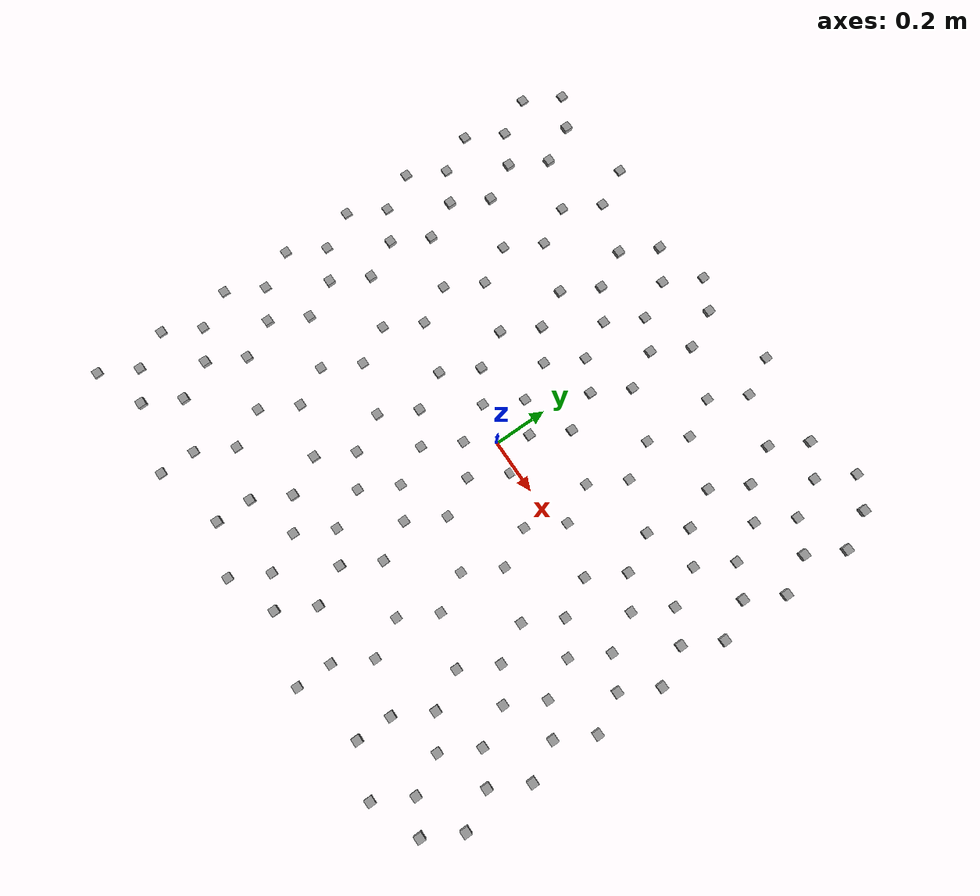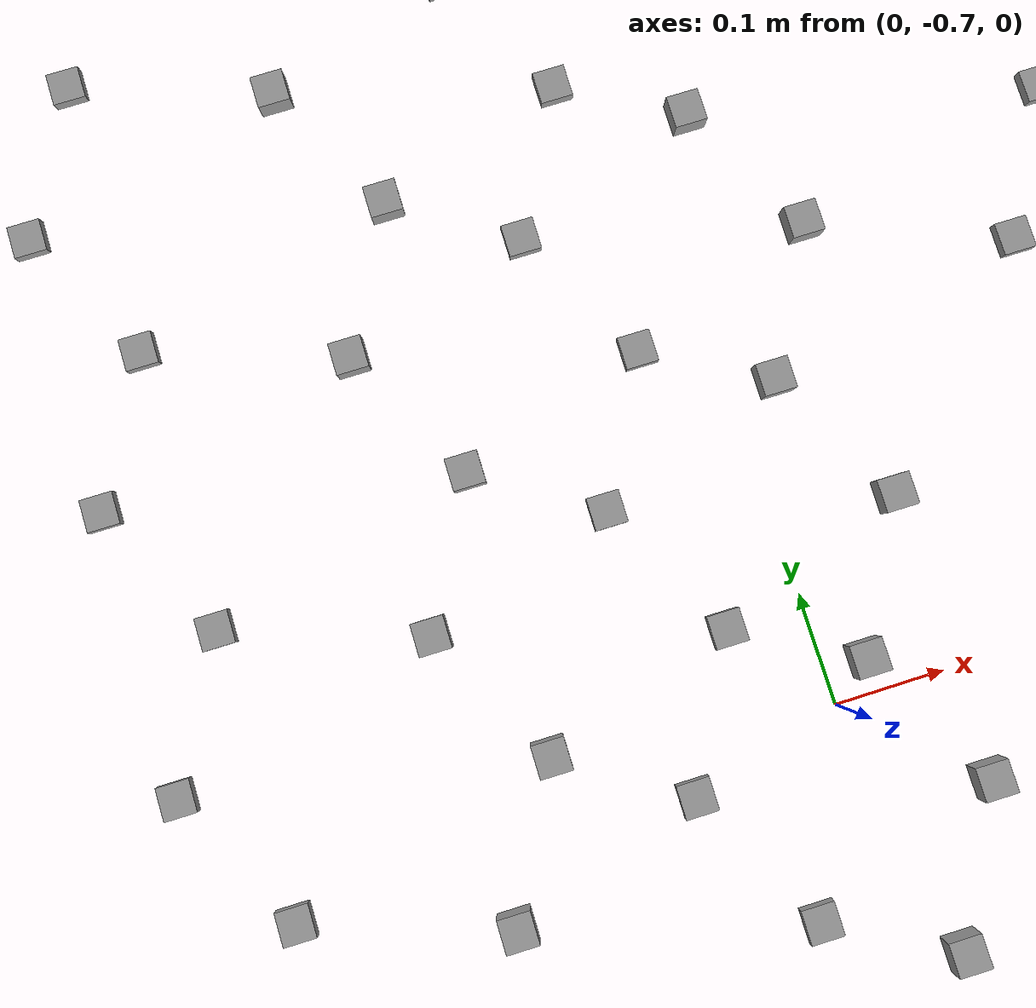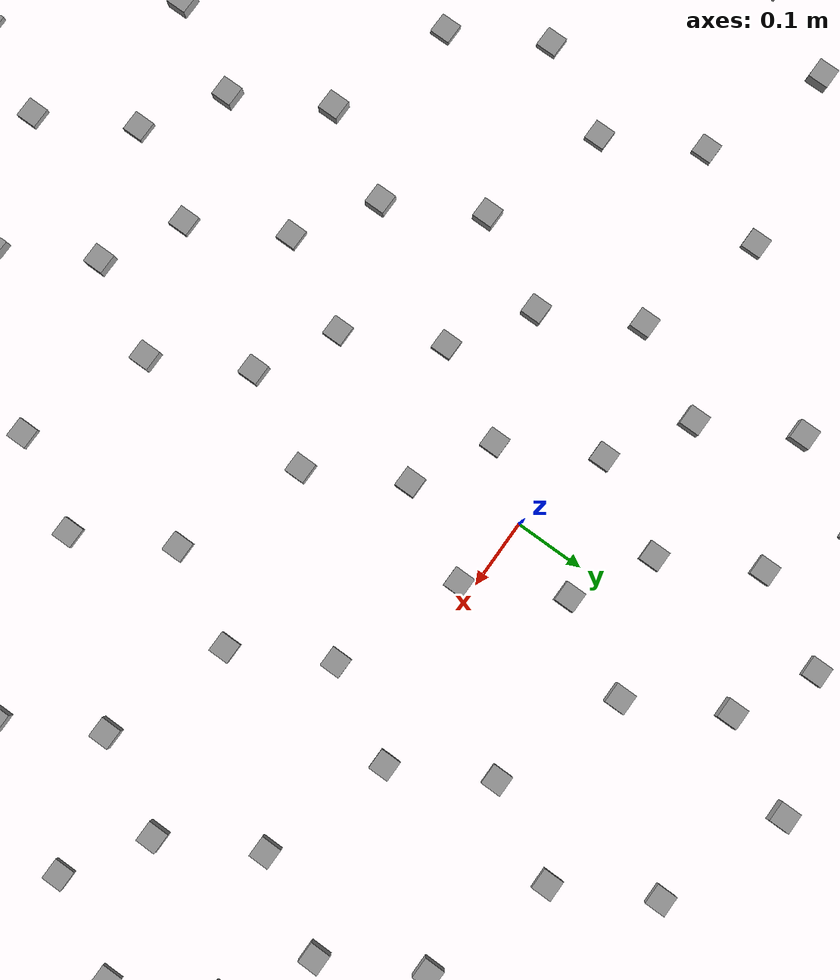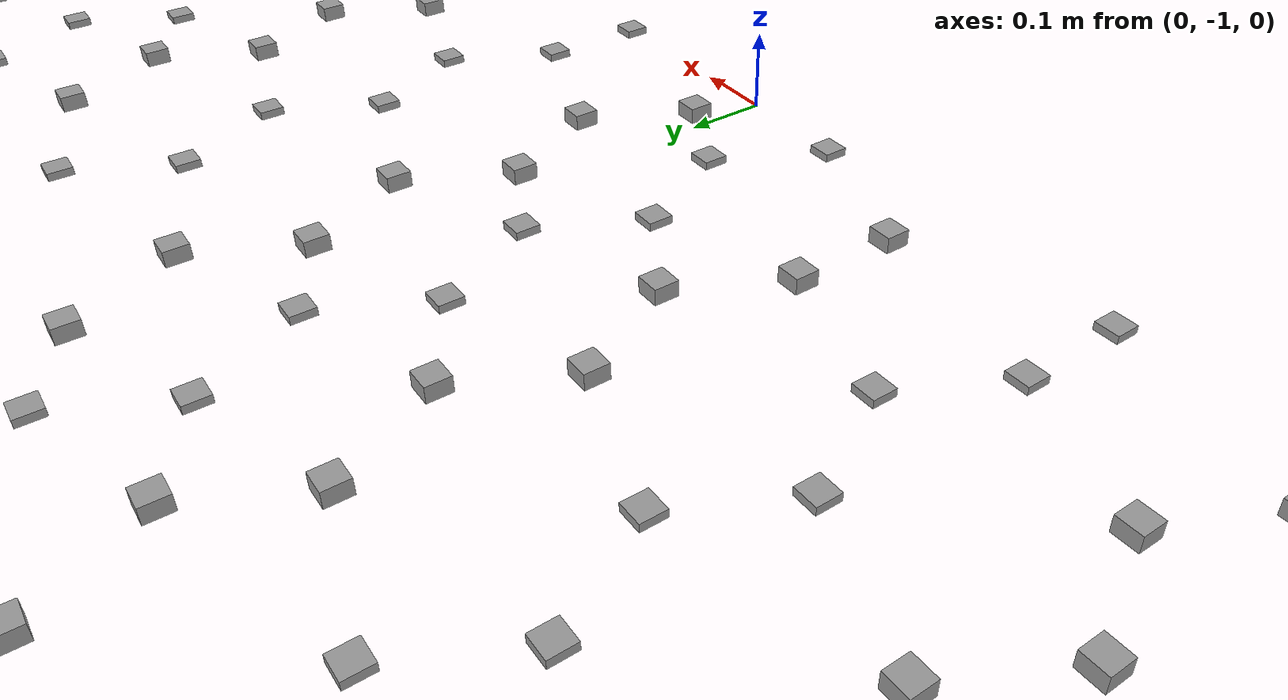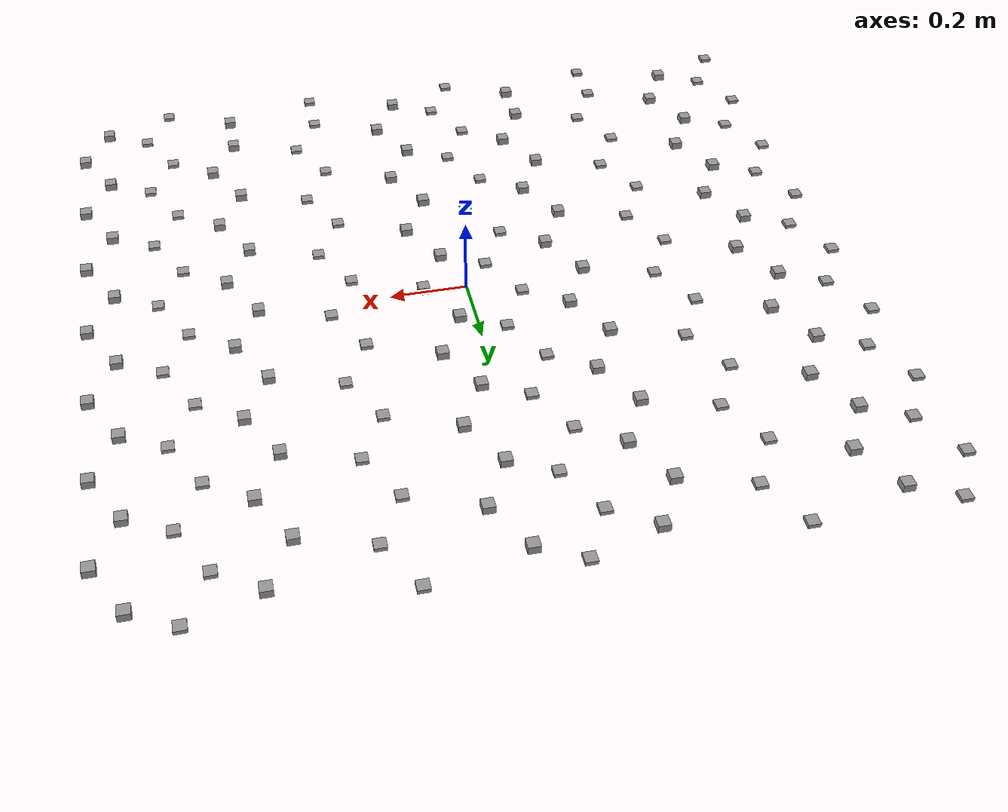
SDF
<sdf version="1.5">
 <world name="default">
  <scene><origin_visual>0</origin_visual><grid>0</grid></scene>
  <physics type="ode">
   <max_step_size>0.003</max_step_size>
   <real_time_update_rate>1000</real_time_update_rate>
   <ode>
    <constraints>
     <erp>0.1</erp>
     <cfm>10e-6</cfm>
     <contact_max_correcting_vel>100</contact_max_correcting_vel>
     <contact_surface_layer>1e-8</contact_surface_layer>
    </constraints>
    <solver><type>quick</type></solver>
   </ode>
  </physics>
  <model name="unit_box_0">
   <pose>-1 -1 0 0 0 0</pose>
   <link name="link">
    <inertial>
     <mass>1</mass>
     <inertia><ixx>0</ixx><ixy>0</ixy><ixz>0</ixz><iyy>0</iyy><iyz>0</iyz><izz>0</izz></inertia>
    </inertial>
    <collision name="collision"><geometry><box><size>0.03 0.03 0.01</size></box></geometry></collision>
    <visual name="visual">
     <geometry><box><size>0.03 0.03 0.01</size></box></geometry>
     <material>
      <script><name>Gazebo/Grey</name><uri>file://media/materials/scripts/gazebo.material</uri></script>
     </material>
    </visual>
   </link>
  </model>
  <model name="unit_box_1">
   <pose>-0.93 -0.87 0 0 0 0</pose>
   <link name="link">
    <inertial>
     <mass>1</mass>
     <inertia><ixx>0</ixx><ixy>0</ixy><ixz>0</ixz><iyy>0</iyy><iyz>0</iyz><izz>0</izz></inertia>
    </inertial>
    <collision name="collision"><geometry><box><size>0.03 0.03 0.01</size></box></geometry></collision>
    <visual name="visual">
     <geometry><box><size>0.03 0.03 0.01</size></box></geometry>
     <material>
      <script><name>Gazebo/Grey</name><uri>file://media/materials/scripts/gazebo.material</uri></script>
     </material>
    </visual>
   </link>
  </model>
  <model name="unit_box_2">
   <pose>-1 -0.74 0 0 0 0</pose>
   <link name="link">
    <inertial>
     <mass>1</mass>
     <inertia><ixx>0</ixx><ixy>0</ixy><ixz>0</ixz><iyy>0</iyy><iyz>0</iyz><izz>0</izz></inertia>
    </inertial>
    <collision name="collision"><geometry><box><size>0.03 0.03 0.01</size></box></geometry></collision>
    <visual name="visual">
     <geometry><box><size>0.03 0.03 0.01</size></box></geometry>
     <material>
      <script><name>Gazebo/Grey</name><uri>file://media/materials/scripts/gazebo.material</uri></script>
     </material>
    </visual>
   </link>
  </model>
  <model name="unit_box_3">
   <pose>-0.93 -0.61 0 0 0 0</pose>
   <link name="link">
    <inertial>
     <mass>1</mass>
     <inertia><ixx>0</ixx><ixy>0</ixy><ixz>0</ixz><iyy>0</iyy><iyz>0</iyz><izz>0</izz></inertia>
    </inertial>
    <collision name="collision"><geometry><box><size>0.03 0.03 0.01</size></box></geometry></collision>
    <visual name="visual">
     <geometry><box><size>0.03 0.03 0.01</size></box></geometry>
     <material>
      <script><name>Gazebo/Grey</name><uri>file://media/materials/scripts/gazebo.material</uri></script>
     </material>
    </visual>
   </link>
  </model>
  <model name="unit_box_4">
   <pose>-1 -0.48 0 0 0 0</pose>
   <link name="link">
    <inertial>
     <mass>1</mass>
     <inertia><ixx>0</ixx><ixy>0</ixy><ixz>0</ixz><iyy>0</iyy><iyz>0</iyz><izz>0</izz></inertia>
    </inertial>
    <collision name="collision"><geometry><box><size>0.03 0.03 0.01</size></box></geometry></collision>
    <visual name="visual">
     <geometry><box><size>0.03 0.03 0.01</size></box></geometry>
     <material>
      <script><name>Gazebo/Grey</name><uri>file://media/materials/scripts/gazebo.material</uri></script>
     </material>
    </visual>
   </link>
  </model>
  <model name="unit_box_5">
   <pose>-0.93 -0.35 0 0 0 0</pose>
   <link name="link">
    <inertial>
     <mass>1</mass>
     <inertia><ixx>0</ixx><ixy>0</ixy><ixz>0</ixz><iyy>0</iyy><iyz>0</iyz><izz>0</izz></inertia>
    </inertial>
    <collision name="collision"><geometry><box><size>0.03 0.03 0.01</size></box></geometry></collision>
    <visual name="visual">
     <geometry><box><size>0.03 0.03 0.01</size></box></geometry>
     <material>
      <script><name>Gazebo/Grey</name><uri>file://media/materials/scripts/gazebo.material</uri></script>
     </material>
    </visual>
   </link>
  </model>
  <model name="unit_box_6">
   <pose>-1 -0.22 0 0 0 0</pose>
   <link name="link">
    <inertial>
     <mass>1</mass>
     <inertia><ixx>0</ixx><ixy>0</ixy><ixz>0</ixz><iyy>0</iyy><iyz>0</iyz><izz>0</izz></inertia>
    </inertial>
    <collision name="collision"><geometry><box><size>0.03 0.03 0.01</size></box></geometry></collision>
    <visual name="visual">
     <geometry><box><size>0.03 0.03 0.01</size></box></geometry>
     <material>
      <script><name>Gazebo/Grey</name><uri>file://media/materials/scripts/gazebo.material</uri></script>
     </material>
    </visual>
   </link>
  </model>
  <model name="unit_box_7">
   <pose>-0.93 -0.0899999999999999 0 0 0 0</pose>
   <link name="link">
    <inertial>
     <mass>1</mass>
     <inertia><ixx>0</ixx><ixy>0</ixy><ixz>0</ixz><iyy>0</iyy><iyz>0</iyz><izz>0</izz></inertia>
    </inertial>
    <collision name="collision"><geometry><box><size>0.03 0.03 0.01</size></box></geometry></collision>
    <visual name="visual">
     <geometry><box><size>0.03 0.03 0.01</size></box></geometry>
     <material>
      <script><name>Gazebo/Grey</name><uri>file://media/materials/scripts/gazebo.material</uri></script>
     </material>
    </visual>
   </link>
  </model>
  <model name="unit_box_8">
   <pose>-1 0.0400000000000001 0 0 0 0</pose>
   <link name="link">
    <inertial>
     <mass>1</mass>
     <inertia><ixx>0</ixx><ixy>0</ixy><ixz>0</ixz><iyy>0</iyy><iyz>0</iyz><izz>0</izz></inertia>
    </inertial>
    <collision name="collision"><geometry><box><size>0.03 0.03 0.01</size></box></geometry></collision>
    <visual name="visual">
     <geometry><box><size>0.03 0.03 0.01</size></box></geometry>
     <material>
      <script><name>Gazebo/Grey</name><uri>file://media/materials/scripts/gazebo.material</uri></script>
     </material>
    </visual>
   </link>
  </model>
  <model name="unit_box_9">
   <pose>-0.93 0.17 0 0 0 0</pose>
   <link name="link">
    <inertial>
     <mass>1</mass>
     <inertia><ixx>0</ixx><ixy>0</ixy><ixz>0</ixz><iyy>0</iyy><iyz>0</iyz><izz>0</izz></inertia>
    </inertial>
    <collision name="collision"><geometry><box><size>0.03 0.03 0.01</size></box></geometry></collision>
    <visual name="visual">
     <geometry><box><size>0.03 0.03 0.01</size></box></geometry>
     <material>
      <script><name>Gazebo/Grey</name><uri>file://media/materials/scripts/gazebo.material</uri></script>
     </material>
    </visual>
   </link>
  </model>
  <model name="unit_box_10">
   <pose>-1 0.3 0 0 0 0</pose>
   <link name="link">
    <inertial>
     <mass>1</mass>
     <inertia><ixx>0</ixx><ixy>0</ixy><ixz>0</ixz><iyy>0</iyy><iyz>0</iyz><izz>0</izz></inertia>
    </inertial>
    <collision name="collision"><geometry><box><size>0.03 0.03 0.01</size></box></geometry></collision>
    <visual name="visual">
     <geometry><box><size>0.03 0.03 0.01</size></box></geometry>
     <material>
      <script><name>Gazebo/Grey</name><uri>file://media/materials/scripts/gazebo.material</uri></script>
     </material>
    </visual>
   </link>
  </model>
  <model name="unit_box_11">
   <pose>-0.93 0.43 0 0 0 0</pose>
   <link name="link">
    <inertial>
     <mass>1</mass>
     <inertia><ixx>0</ixx><ixy>0</ixy><ixz>0</ixz><iyy>0</iyy><iyz>0</iyz><izz>0</izz></inertia>
    </inertial>
    <collision name="collision"><geometry><box><size>0.03 0.03 0.01</size></box></geometry></collision>
    <visual name="visual">
     <geometry><box><size>0.03 0.03 0.01</size></box></geometry>
     <material>
      <script><name>Gazebo/Grey</name><uri>file://media/materials/scripts/gazebo.material</uri></script>
     </material>
    </visual>
   </link>
  </model>
  <model name="unit_box_12">
   <pose>-1 0.56 0 0 0 0</pose>
   <link name="link">
    <inertial>
     <mass>1</mass>
     <inertia><ixx>0</ixx><ixy>0</ixy><ixz>0</ixz><iyy>0</iyy><iyz>0</iyz><izz>0</izz></inertia>
    </inertial>
    <collision name="collision"><geometry><box><size>0.03 0.03 0.01</size></box></geometry></collision>
    <visual name="visual">
     <geometry><box><size>0.03 0.03 0.01</size></box></geometry>
     <material>
      <script><name>Gazebo/Grey</name><uri>file://media/materials/scripts/gazebo.material</uri></script>
     </material>
    </visual>
   </link>
  </model>
  <model name="unit_box_13">
   <pose>-0.93 0.69 0 0 0 0</pose>
   <link name="link">
    <inertial>
     <mass>1</mass>
     <inertia><ixx>0</ixx><ixy>0</ixy><ixz>0</ixz><iyy>0</iyy><iyz>0</iyz><izz>0</izz></inertia>
    </inertial>
    <collision name="collision"><geometry><box><size>0.03 0.03 0.01</size></box></geometry></collision>
    <visual name="visual">
     <geometry><box><size>0.03 0.03 0.01</size></box></geometry>
     <material>
      <script><name>Gazebo/Grey</name><uri>file://media/materials/scripts/gazebo.material</uri></script>
     </material>
    </visual>
   </link>
  </model>
  <model name="unit_box_14">
   <pose>-1 0.82 0 0 0 0</pose>
   <link name="link">
    <inertial>
     <mass>1</mass>
     <inertia><ixx>0</ixx><ixy>0</ixy><ixz>0</ixz><iyy>0</iyy><iyz>0</iyz><izz>0</izz></inertia>
    </inertial>
    <collision name="collision"><geometry><box><size>0.03 0.03 0.01</size></box></geometry></collision>
    <visual name="visual">
     <geometry><box><size>0.03 0.03 0.01</size></box></geometry>
     <material>
      <script><name>Gazebo/Grey</name><uri>file://media/materials/scripts/gazebo.material</uri></script>
     </material>
    </visual>
   </link>
  </model>
  <model name="unit_box_15">
   <pose>-0.93 0.95 0 0 0 0</pose>
   <link name="link">
    <inertial>
     <mass>1</mass>
     <inertia><ixx>0</ixx><ixy>0</ixy><ixz>0</ixz><iyy>0</iyy><iyz>0</iyz><izz>0</izz></inertia>
    </inertial>
    <collision name="collision"><geometry><box><size>0.03 0.03 0.01</size></box></geometry></collision>
    <visual name="visual">
     <geometry><box><size>0.03 0.03 0.01</size></box></geometry>
     <material>
      <script><name>Gazebo/Grey</name><uri>file://media/materials/scripts/gazebo.material</uri></script>
     </material>
    </visual>
   </link>
  </model>
  <model name="unit_box_16">
   <pose>-0.82 -0.93 0 0 0 0</pose>
   <link name="link">
    <inertial>
     <mass>1</mass>
     <inertia><ixx>0</ixx><ixy>0</ixy><ixz>0</ixz><iyy>0</iyy><iyz>0</iyz><izz>0</izz></inertia>
    </inertial>
    <collision name="collision"><geometry><box><size>0.03 0.03 0.02</size></box></geometry></collision>
    <visual name="visual">
     <geometry><box><size>0.03 0.03 0.02</size></box></geometry>
     <material>
      <script><name>Gazebo/Grey</name><uri>file://media/materials/scripts/gazebo.material</uri></script>
     </material>
    </visual>
   </link>
  </model>
  <model name="unit_box_17">
   <pose>-0.75 -0.8 0 0 0 0</pose>
   <link name="link">
    <inertial>
     <mass>1</mass>
     <inertia><ixx>0</ixx><ixy>0</ixy><ixz>0</ixz><iyy>0</iyy><iyz>0</iyz><izz>0</izz></inertia>
    </inertial>
    <collision name="collision"><geometry><box><size>0.03 0.03 0.02</size></box></geometry></collision>
    <visual name="visual">
     <geometry><box><size>0.03 0.03 0.02</size></box></geometry>
     <material>
      <script><name>Gazebo/Grey</name><uri>file://media/materials/scripts/gazebo.material</uri></script>
     </material>
    </visual>
   </link>
  </model>
  <model name="unit_box_18">
   <pose>-0.82 -0.67 0 0 0 0</pose>
   <link name="link">
    <inertial>
     <mass>1</mass>
     <inertia><ixx>0</ixx><ixy>0</ixy><ixz>0</ixz><iyy>0</iyy><iyz>0</iyz><izz>0</izz></inertia>
    </inertial>
    <collision name="collision"><geometry><box><size>0.03 0.03 0.02</size></box></geometry></collision>
    <visual name="visual">
     <geometry><box><size>0.03 0.03 0.02</size></box></geometry>
     <material>
      <script><name>Gazebo/Grey</name><uri>file://media/materials/scripts/gazebo.material</uri></script>
     </material>
    </visual>
   </link>
  </model>
  <model name="unit_box_19">
   <pose>-0.75 -0.54 0 0 0 0</pose>
   <link name="link">
    <inertial>
     <mass>1</mass>
     <inertia><ixx>0</ixx><ixy>0</ixy><ixz>0</ixz><iyy>0</iyy><iyz>0</iyz><izz>0</izz></inertia>
    </inertial>
    <collision name="collision"><geometry><box><size>0.03 0.03 0.02</size></box></geometry></collision>
    <visual name="visual">
     <geometry><box><size>0.03 0.03 0.02</size></box></geometry>
     <material>
      <script><name>Gazebo/Grey</name><uri>file://media/materials/scripts/gazebo.material</uri></script>
     </material>
    </visual>
   </link>
  </model>
  <model name="unit_box_20">
   <pose>-0.82 -0.41 0 0 0 0</pose>
   <link name="link">
    <inertial>
     <mass>1</mass>
     <inertia><ixx>0</ixx><ixy>0</ixy><ixz>0</ixz><iyy>0</iyy><iyz>0</iyz><izz>0</izz></inertia>
    </inertial>
    <collision name="collision"><geometry><box><size>0.03 0.03 0.02</size></box></geometry></collision>
    <visual name="visual">
     <geometry><box><size>0.03 0.03 0.02</size></box></geometry>
     <material>
      <script><name>Gazebo/Grey</name><uri>file://media/materials/scripts/gazebo.material</uri></script>
     </material>
    </visual>
   </link>
  </model>
  <model name="unit_box_21">
   <pose>-0.75 -0.28 0 0 0 0</pose>
   <link name="link">
    <inertial>
     <mass>1</mass>
     <inertia><ixx>0</ixx><ixy>0</ixy><ixz>0</ixz><iyy>0</iyy><iyz>0</iyz><izz>0</izz></inertia>
    </inertial>
    <collision name="collision"><geometry><box><size>0.03 0.03 0.02</size></box></geometry></collision>
    <visual name="visual">
     <geometry><box><size>0.03 0.03 0.02</size></box></geometry>
     <material>
      <script><name>Gazebo/Grey</name><uri>file://media/materials/scripts/gazebo.material</uri></script>
     </material>
    </visual>
   </link>
  </model>
  <model name="unit_box_22">
   <pose>-0.82 -0.15 0 0 0 0</pose>
   <link name="link">
    <inertial>
     <mass>1</mass>
     <inertia><ixx>0</ixx><ixy>0</ixy><ixz>0</ixz><iyy>0</iyy><iyz>0</iyz><izz>0</izz></inertia>
    </inertial>
    <collision name="collision"><geometry><box><size>0.03 0.03 0.02</size></box></geometry></collision>
    <visual name="visual">
     <geometry><box><size>0.03 0.03 0.02</size></box></geometry>
     <material>
      <script><name>Gazebo/Grey</name><uri>file://media/materials/scripts/gazebo.material</uri></script>
     </material>
    </visual>
   </link>
  </model>
  <model name="unit_box_23">
   <pose>-0.75 -0.02 0 0 0 0</pose>
   <link name="link">
    <inertial>
     <mass>1</mass>
     <inertia><ixx>0</ixx><ixy>0</ixy><ixz>0</ixz><iyy>0</iyy><iyz>0</iyz><izz>0</izz></inertia>
    </inertial>
    <collision name="collision"><geometry><box><size>0.03 0.03 0.02</size></box></geometry></collision>
    <visual name="visual">
     <geometry><box><size>0.03 0.03 0.02</size></box></geometry>
     <material>
      <script><name>Gazebo/Grey</name><uri>file://media/materials/scripts/gazebo.material</uri></script>
     </material>
    </visual>
   </link>
  </model>
  <model name="unit_box_24">
   <pose>-0.82 0.11 0 0 0 0</pose>
   <link name="link">
    <inertial>
     <mass>1</mass>
     <inertia><ixx>0</ixx><ixy>0</ixy><ixz>0</ixz><iyy>0</iyy><iyz>0</iyz><izz>0</izz></inertia>
    </inertial>
    <collision name="collision"><geometry><box><size>0.03 0.03 0.02</size></box></geometry></collision>
    <visual name="visual">
     <geometry><box><size>0.03 0.03 0.02</size></box></geometry>
     <material>
      <script><name>Gazebo/Grey</name><uri>file://media/materials/scripts/gazebo.material</uri></script>
     </material>
    </visual>
   </link>
  </model>
  <model name="unit_box_25">
   <pose>-0.75 0.24 0 0 0 0</pose>
   <link name="link">
    <inertial>
     <mass>1</mass>
     <inertia><ixx>0</ixx><ixy>0</ixy><ixz>0</ixz><iyy>0</iyy><iyz>0</iyz><izz>0</izz></inertia>
    </inertial>
    <collision name="collision"><geometry><box><size>0.03 0.03 0.02</size></box></geometry></collision>
    <visual name="visual">
     <geometry><box><size>0.03 0.03 0.02</size></box></geometry>
     <material>
      <script><name>Gazebo/Grey</name><uri>file://media/materials/scripts/gazebo.material</uri></script>
     </material>
    </visual>
   </link>
  </model>
  <model name="unit_box_26">
   <pose>-0.82 0.37 0 0 0 0</pose>
   <link name="link">
    <inertial>
     <mass>1</mass>
     <inertia><ixx>0</ixx><ixy>0</ixy><ixz>0</ixz><iyy>0</iyy><iyz>0</iyz><izz>0</izz></inertia>
    </inertial>
    <collision name="collision"><geometry><box><size>0.03 0.03 0.02</size></box></geometry></collision>
    <visual name="visual">
     <geometry><box><size>0.03 0.03 0.02</size></box></geometry>
     <material>
      <script><name>Gazebo/Grey</name><uri>file://media/materials/scripts/gazebo.material</uri></script>
     </material>
    </visual>
   </link>
  </model>
  <model name="unit_box_27">
   <pose>-0.75 0.5 0 0 0 0</pose>
   <link name="link">
    <inertial>
     <mass>1</mass>
     <inertia><ixx>0</ixx><ixy>0</ixy><ixz>0</ixz><iyy>0</iyy><iyz>0</iyz><izz>0</izz></inertia>
    </inertial>
    <collision name="collision"><geometry><box><size>0.03 0.03 0.02</size></box></geometry></collision>
    <visual name="visual">
     <geometry><box><size>0.03 0.03 0.02</size></box></geometry>
     <material>
      <script><name>Gazebo/Grey</name><uri>file://media/materials/scripts/gazebo.material</uri></script>
     </material>
    </visual>
   </link>
  </model>
  <model name="unit_box_28">
   <pose>-0.82 0.63 0 0 0 0</pose>
   <link name="link">
    <inertial>
     <mass>1</mass>
     <inertia><ixx>0</ixx><ixy>0</ixy><ixz>0</ixz><iyy>0</iyy><iyz>0</iyz><izz>0</izz></inertia>
    </inertial>
    <collision name="collision"><geometry><box><size>0.03 0.03 0.02</size></box></geometry></collision>
    <visual name="visual">
     <geometry><box><size>0.03 0.03 0.02</size></box></geometry>
     <material>
      <script><name>Gazebo/Grey</name><uri>file://media/materials/scripts/gazebo.material</uri></script>
     </material>
    </visual>
   </link>
  </model>
  <model name="unit_box_29">
   <pose>-0.75 0.76 0 0 0 0</pose>
   <link name="link">
    <inertial>
     <mass>1</mass>
     <inertia><ixx>0</ixx><ixy>0</ixy><ixz>0</ixz><iyy>0</iyy><iyz>0</iyz><izz>0</izz></inertia>
    </inertial>
    <collision name="collision"><geometry><box><size>0.03 0.03 0.02</size></box></geometry></collision>
    <visual name="visual">
     <geometry><box><size>0.03 0.03 0.02</size></box></geometry>
     <material>
      <script><name>Gazebo/Grey</name><uri>file://media/materials/scripts/gazebo.material</uri></script>
     </material>
    </visual>
   </link>
  </model>
  <model name="unit_box_30">
   <pose>-0.82 0.89 0 0 0 0</pose>
   <link name="link">
    <inertial>
     <mass>1</mass>
     <inertia><ixx>0</ixx><ixy>0</ixy><ixz>0</ixz><iyy>0</iyy><iyz>0</iyz><izz>0</izz></inertia>
    </inertial>
    <collision name="collision"><geometry><box><size>0.03 0.03 0.02</size></box></geometry></collision>
    <visual name="visual">
     <geometry><box><size>0.03 0.03 0.02</size></box></geometry>
     <material>
      <script><name>Gazebo/Grey</name><uri>file://media/materials/scripts/gazebo.material</uri></script>
     </material>
    </visual>
   </link>
  </model>
  <model name="unit_box_31">
   <pose>-0.57 -1 0 0 0 0</pose>
   <link name="link">
    <inertial>
     <mass>1</mass>
     <inertia><ixx>0</ixx><ixy>0</ixy><ixz>0</ixz><iyy>0</iyy><iyz>0</iyz><izz>0</izz></inertia>
    </inertial>
    <collision name="collision"><geometry><box><size>0.03 0.03 0.01</size></box></geometry></collision>
    <visual name="visual">
     <geometry><box><size>0.03 0.03 0.01</size></box></geometry>
     <material>
      <script><name>Gazebo/Grey</name><uri>file://media/materials/scripts/gazebo.material</uri></script>
     </material>
    </visual>
   </link>
  </model>
  <model name="unit_box_32">
   <pose>-0.57 -0.87 0 0 0 0</pose>
   <link name="link">
    <inertial>
     <mass>1</mass>
     <inertia><ixx>0</ixx><ixy>0</ixy><ixz>0</ixz><iyy>0</iyy><iyz>0</iyz><izz>0</izz></inertia>
    </inertial>
    <collision name="collision"><geometry><box><size>0.03 0.03 0.01</size></box></geometry></collision>
    <visual name="visual">
     <geometry><box><size>0.03 0.03 0.01</size></box></geometry>
     <material>
      <script><name>Gazebo/Grey</name><uri>file://media/materials/scripts/gazebo.material</uri></script>
     </material>
    </visual>
   </link>
  </model>
  <model name="unit_box_33">
   <pose>-0.5 -0.74 0 0 0 0</pose>
   <link name="link">
    <inertial>
     <mass>1</mass>
     <inertia><ixx>0</ixx><ixy>0</ixy><ixz>0</ixz><iyy>0</iyy><iyz>0</iyz><izz>0</izz></inertia>
    </inertial>
    <collision name="collision"><geometry><box><size>0.03 0.03 0.01</size></box></geometry></collision>
    <visual name="visual">
     <geometry><box><size>0.03 0.03 0.01</size></box></geometry>
     <material>
      <script><name>Gazebo/Grey</name><uri>file://media/materials/scripts/gazebo.material</uri></script>
     </material>
    </visual>
   </link>
  </model>
  <model name="unit_box_34">
   <pose>-0.57 -0.61 0 0 0 0</pose>
   <link name="link">
    <inertial>
     <mass>1</mass>
     <inertia><ixx>0</ixx><ixy>0</ixy><ixz>0</ixz><iyy>0</iyy><iyz>0</iyz><izz>0</izz></inertia>
    </inertial>
    <collision name="collision"><geometry><box><size>0.03 0.03 0.01</size></box></geometry></collision>
    <visual name="visual">
     <geometry><box><size>0.03 0.03 0.01</size></box></geometry>
     <material>
      <script><name>Gazebo/Grey</name><uri>file://media/materials/scripts/gazebo.material</uri></script>
     </material>
    </visual>
   </link>
  </model>
  <model name="unit_box_35">
   <pose>-0.5 -0.48 0 0 0 0</pose>
   <link name="link">
    <inertial>
     <mass>1</mass>
     <inertia><ixx>0</ixx><ixy>0</ixy><ixz>0</ixz><iyy>0</iyy><iyz>0</iyz><izz>0</izz></inertia>
    </inertial>
    <collision name="collision"><geometry><box><size>0.03 0.03 0.01</size></box></geometry></collision>
    <visual name="visual">
     <geometry><box><size>0.03 0.03 0.01</size></box></geometry>
     <material>
      <script><name>Gazebo/Grey</name><uri>file://media/materials/scripts/gazebo.material</uri></script>
     </material>
    </visual>
   </link>
  </model>
  <model name="unit_box_36">
   <pose>-0.57 -0.35 0 0 0 0</pose>
   <link name="link">
    <inertial>
     <mass>1</mass>
     <inertia><ixx>0</ixx><ixy>0</ixy><ixz>0</ixz><iyy>0</iyy><iyz>0</iyz><izz>0</izz></inertia>
    </inertial>
    <collision name="collision"><geometry><box><size>0.03 0.03 0.01</size></box></geometry></collision>
    <visual name="visual">
     <geometry><box><size>0.03 0.03 0.01</size></box></geometry>
     <material>
      <script><name>Gazebo/Grey</name><uri>file://media/materials/scripts/gazebo.material</uri></script>
     </material>
    </visual>
   </link>
  </model>
  <model name="unit_box_37">
   <pose>-0.5 -0.22 0 0 0 0</pose>
   <link name="link">
    <inertial>
     <mass>1</mass>
     <inertia><ixx>0</ixx><ixy>0</ixy><ixz>0</ixz><iyy>0</iyy><iyz>0</iyz><izz>0</izz></inertia>
    </inertial>
    <collision name="collision"><geometry><box><size>0.03 0.03 0.01</size></box></geometry></collision>
    <visual name="visual">
     <geometry><box><size>0.03 0.03 0.01</size></box></geometry>
     <material>
      <script><name>Gazebo/Grey</name><uri>file://media/materials/scripts/gazebo.material</uri></script>
     </material>
    </visual>
   </link>
  </model>
  <model name="unit_box_38">
   <pose>-0.57 -0.0899999999999999 0 0 0 0</pose>
   <link name="link">
    <inertial>
     <mass>1</mass>
     <inertia><ixx>0</ixx><ixy>0</ixy><ixz>0</ixz><iyy>0</iyy><iyz>0</iyz><izz>0</izz></inertia>
    </inertial>
    <collision name="collision"><geometry><box><size>0.03 0.03 0.01</size></box></geometry></collision>
    <visual name="visual">
     <geometry><box><size>0.03 0.03 0.01</size></box></geometry>
     <material>
      <script><name>Gazebo/Grey</name><uri>file://media/materials/scripts/gazebo.material</uri></script>
     </material>
    </visual>
   </link>
  </model>
  <model name="unit_box_39">
   <pose>-0.5 0.0400000000000001 0 0 0 0</pose>
   <link name="link">
    <inertial>
     <mass>1</mass>
     <inertia><ixx>0</ixx><ixy>0</ixy><ixz>0</ixz><iyy>0</iyy><iyz>0</iyz><izz>0</izz></inertia>
    </inertial>
    <collision name="collision"><geometry><box><size>0.03 0.03 0.01</size></box></geometry></collision>
    <visual name="visual">
     <geometry><box><size>0.03 0.03 0.01</size></box></geometry>
     <material>
      <script><name>Gazebo/Grey</name><uri>file://media/materials/scripts/gazebo.material</uri></script>
     </material>
    </visual>
   </link>
  </model>
  <model name="unit_box_40">
   <pose>-0.57 0.17 0 0 0 0</pose>
   <link name="link">
    <inertial>
     <mass>1</mass>
     <inertia><ixx>0</ixx><ixy>0</ixy><ixz>0</ixz><iyy>0</iyy><iyz>0</iyz><izz>0</izz></inertia>
    </inertial>
    <collision name="collision"><geometry><box><size>0.03 0.03 0.01</size></box></geometry></collision>
    <visual name="visual">
     <geometry><box><size>0.03 0.03 0.01</size></box></geometry>
     <material>
      <script><name>Gazebo/Grey</name><uri>file://media/materials/scripts/gazebo.material</uri></script>
     </material>
    </visual>
   </link>
  </model>
  <model name="unit_box_41">
   <pose>-0.5 0.3 0 0 0 0</pose>
   <link name="link">
    <inertial>
     <mass>1</mass>
     <inertia><ixx>0</ixx><ixy>0</ixy><ixz>0</ixz><iyy>0</iyy><iyz>0</iyz><izz>0</izz></inertia>
    </inertial>
    <collision name="collision"><geometry><box><size>0.03 0.03 0.01</size></box></geometry></collision>
    <visual name="visual">
     <geometry><box><size>0.03 0.03 0.01</size></box></geometry>
     <material>
      <script><name>Gazebo/Grey</name><uri>file://media/materials/scripts/gazebo.material</uri></script>
     </material>
    </visual>
   </link>
  </model>
  <model name="unit_box_42">
   <pose>-0.57 0.43 0 0 0 0</pose>
   <link name="link">
    <inertial>
     <mass>1</mass>
     <inertia><ixx>0</ixx><ixy>0</ixy><ixz>0</ixz><iyy>0</iyy><iyz>0</iyz><izz>0</izz></inertia>
    </inertial>
    <collision name="collision"><geometry><box><size>0.03 0.03 0.01</size></box></geometry></collision>
    <visual name="visual">
     <geometry><box><size>0.03 0.03 0.01</size></box></geometry>
     <material>
      <script><name>Gazebo/Grey</name><uri>file://media/materials/scripts/gazebo.material</uri></script>
     </material>
    </visual>
   </link>
  </model>
  <model name="unit_box_43">
   <pose>-0.5 0.56 0 0 0 0</pose>
   <link name="link">
    <inertial>
     <mass>1</mass>
     <inertia><ixx>0</ixx><ixy>0</ixy><ixz>0</ixz><iyy>0</iyy><iyz>0</iyz><izz>0</izz></inertia>
    </inertial>
    <collision name="collision"><geometry><box><size>0.03 0.03 0.01</size></box></geometry></collision>
    <visual name="visual">
     <geometry><box><size>0.03 0.03 0.01</size></box></geometry>
     <material>
      <script><name>Gazebo/Grey</name><uri>file://media/materials/scripts/gazebo.material</uri></script>
     </material>
    </visual>
   </link>
  </model>
  <model name="unit_box_44">
   <pose>-0.57 0.69 0 0 0 0</pose>
   <link name="link">
    <inertial>
     <mass>1</mass>
     <inertia><ixx>0</ixx><ixy>0</ixy><ixz>0</ixz><iyy>0</iyy><iyz>0</iyz><izz>0</izz></inertia>
    </inertial>
    <collision name="collision"><geometry><box><size>0.03 0.03 0.01</size></box></geometry></collision>
    <visual name="visual">
     <geometry><box><size>0.03 0.03 0.01</size></box></geometry>
     <material>
      <script><name>Gazebo/Grey</name><uri>file://media/materials/scripts/gazebo.material</uri></script>
     </material>
    </visual>
   </link>
  </model>
  <model name="unit_box_45">
   <pose>-0.5 0.82 0 0 0 0</pose>
   <link name="link">
    <inertial>
     <mass>1</mass>
     <inertia><ixx>0</ixx><ixy>0</ixy><ixz>0</ixz><iyy>0</iyy><iyz>0</iyz><izz>0</izz></inertia>
    </inertial>
    <collision name="collision"><geometry><box><size>0.03 0.03 0.01</size></box></geometry></collision>
    <visual name="visual">
     <geometry><box><size>0.03 0.03 0.01</size></box></geometry>
     <material>
      <script><name>Gazebo/Grey</name><uri>file://media/materials/scripts/gazebo.material</uri></script>
     </material>
    </visual>
   </link>
  </model>
  <model name="unit_box_46">
   <pose>-0.57 0.95 0 0 0 0</pose>
   <link name="link">
    <inertial>
     <mass>1</mass>
     <inertia><ixx>0</ixx><ixy>0</ixy><ixz>0</ixz><iyy>0</iyy><iyz>0</iyz><izz>0</izz></inertia>
    </inertial>
    <collision name="collision"><geometry><box><size>0.03 0.03 0.01</size></box></geometry></collision>
    <visual name="visual">
     <geometry><box><size>0.03 0.03 0.01</size></box></geometry>
     <material>
      <script><name>Gazebo/Grey</name><uri>file://media/materials/scripts/gazebo.material</uri></script>
     </material>
    </visual>
   </link>
  </model>
  <model name="unit_box_47">
   <pose>-0.32 -0.93 0 0 0 0</pose>
   <link name="link">
    <inertial>
     <mass>1</mass>
     <inertia><ixx>0</ixx><ixy>0</ixy><ixz>0</ixz><iyy>0</iyy><iyz>0</iyz><izz>0</izz></inertia>
    </inertial>
    <collision name="collision"><geometry><box><size>0.03 0.03 0.02</size></box></geometry></collision>
    <visual name="visual">
     <geometry><box><size>0.03 0.03 0.02</size></box></geometry>
     <material>
      <script><name>Gazebo/Grey</name><uri>file://media/materials/scripts/gazebo.material</uri></script>
     </material>
    </visual>
   </link>
  </model>
  <model name="unit_box_48">
   <pose>-0.32 -0.8 0 0 0 0</pose>
   <link name="link">
    <inertial>
     <mass>1</mass>
     <inertia><ixx>0</ixx><ixy>0</ixy><ixz>0</ixz><iyy>0</iyy><iyz>0</iyz><izz>0</izz></inertia>
    </inertial>
    <collision name="collision"><geometry><box><size>0.03 0.03 0.02</size></box></geometry></collision>
    <visual name="visual">
     <geometry><box><size>0.03 0.03 0.02</size></box></geometry>
     <material>
      <script><name>Gazebo/Grey</name><uri>file://media/materials/scripts/gazebo.material</uri></script>
     </material>
    </visual>
   </link>
  </model>
  <model name="unit_box_49">
   <pose>-0.25 -0.67 0 0 0 0</pose>
   <link name="link">
    <inertial>
     <mass>1</mass>
     <inertia><ixx>0</ixx><ixy>0</ixy><ixz>0</ixz><iyy>0</iyy><iyz>0</iyz><izz>0</izz></inertia>
    </inertial>
    <collision name="collision"><geometry><box><size>0.03 0.03 0.02</size></box></geometry></collision>
    <visual name="visual">
     <geometry><box><size>0.03 0.03 0.02</size></box></geometry>
     <material>
      <script><name>Gazebo/Grey</name><uri>file://media/materials/scripts/gazebo.material</uri></script>
     </material>
    </visual>
   </link>
  </model>
  <model name="unit_box_50">
   <pose>-0.32 -0.54 0 0 0 0</pose>
   <link name="link">
    <inertial>
     <mass>1</mass>
     <inertia><ixx>0</ixx><ixy>0</ixy><ixz>0</ixz><iyy>0</iyy><iyz>0</iyz><izz>0</izz></inertia>
    </inertial>
    <collision name="collision"><geometry><box><size>0.03 0.03 0.02</size></box></geometry></collision>
    <visual name="visual">
     <geometry><box><size>0.03 0.03 0.02</size></box></geometry>
     <material>
      <script><name>Gazebo/Grey</name><uri>file://media/materials/scripts/gazebo.material</uri></script>
     </material>
    </visual>
   </link>
  </model>
  <model name="unit_box_51">
   <pose>-0.25 -0.41 0 0 0 0</pose>
   <link name="link">
    <inertial>
     <mass>1</mass>
     <inertia><ixx>0</ixx><ixy>0</ixy><ixz>0</ixz><iyy>0</iyy><iyz>0</iyz><izz>0</izz></inertia>
    </inertial>
    <collision name="collision"><geometry><box><size>0.03 0.03 0.02</size></box></geometry></collision>
    <visual name="visual">
     <geometry><box><size>0.03 0.03 0.02</size></box></geometry>
     <material>
      <script><name>Gazebo/Grey</name><uri>file://media/materials/scripts/gazebo.material</uri></script>
     </material>
    </visual>
   </link>
  </model>
  <model name="unit_box_52">
   <pose>-0.32 -0.28 0 0 0 0</pose>
   <link name="link">
    <inertial>
     <mass>1</mass>
     <inertia><ixx>0</ixx><ixy>0</ixy><ixz>0</ixz><iyy>0</iyy><iyz>0</iyz><izz>0</izz></inertia>
    </inertial>
    <collision name="collision"><geometry><box><size>0.03 0.03 0.02</size></box></geometry></collision>
    <visual name="visual">
     <geometry><box><size>0.03 0.03 0.02</size></box></geometry>
     <material>
      <script><name>Gazebo/Grey</name><uri>file://media/materials/scripts/gazebo.material</uri></script>
     </material>
    </visual>
   </link>
  </model>
  <model name="unit_box_53">
   <pose>-0.25 -0.15 0 0 0 0</pose>
   <link name="link">
    <inertial>
     <mass>1</mass>
     <inertia><ixx>0</ixx><ixy>0</ixy><ixz>0</ixz><iyy>0</iyy><iyz>0</iyz><izz>0</izz></inertia>
    </inertial>
    <collision name="collision"><geometry><box><size>0.03 0.03 0.02</size></box></geometry></collision>
    <visual name="visual">
     <geometry><box><size>0.03 0.03 0.02</size></box></geometry>
     <material>
      <script><name>Gazebo/Grey</name><uri>file://media/materials/scripts/gazebo.material</uri></script>
     </material>
    </visual>
   </link>
  </model>
  <model name="unit_box_54">
   <pose>-0.32 -0.02 0 0 0 0</pose>
   <link name="link">
    <inertial>
     <mass>1</mass>
     <inertia><ixx>0</ixx><ixy>0</ixy><ixz>0</ixz><iyy>0</iyy><iyz>0</iyz><izz>0</izz></inertia>
    </inertial>
    <collision name="collision"><geometry><box><size>0.03 0.03 0.02</size></box></geometry></collision>
    <visual name="visual">
     <geometry><box><size>0.03 0.03 0.02</size></box></geometry>
     <material>
      <script><name>Gazebo/Grey</name><uri>file://media/materials/scripts/gazebo.material</uri></script>
     </material>
    </visual>
   </link>
  </model>
  <model name="unit_box_55">
   <pose>-0.25 0.11 0 0 0 0</pose>
   <link name="link">
    <inertial>
     <mass>1</mass>
     <inertia><ixx>0</ixx><ixy>0</ixy><ixz>0</ixz><iyy>0</iyy><iyz>0</iyz><izz>0</izz></inertia>
    </inertial>
    <collision name="collision"><geometry><box><size>0.03 0.03 0.02</size></box></geometry></collision>
    <visual name="visual">
     <geometry><box><size>0.03 0.03 0.02</size></box></geometry>
     <material>
      <script><name>Gazebo/Grey</name><uri>file://media/materials/scripts/gazebo.material</uri></script>
     </material>
    </visual>
   </link>
  </model>
  <model name="unit_box_56">
   <pose>-0.32 0.24 0 0 0 0</pose>
   <link name="link">
    <inertial>
     <mass>1</mass>
     <inertia><ixx>0</ixx><ixy>0</ixy><ixz>0</ixz><iyy>0</iyy><iyz>0</iyz><izz>0</izz></inertia>
    </inertial>
    <collision name="collision"><geometry><box><size>0.03 0.03 0.02</size></box></geometry></collision>
    <visual name="visual">
     <geometry><box><size>0.03 0.03 0.02</size></box></geometry>
     <material>
      <script><name>Gazebo/Grey</name><uri>file://media/materials/scripts/gazebo.material</uri></script>
     </material>
    </visual>
   </link>
  </model>
  <model name="unit_box_57">
   <pose>-0.25 0.37 0 0 0 0</pose>
   <link name="link">
    <inertial>
     <mass>1</mass>
     <inertia><ixx>0</ixx><ixy>0</ixy><ixz>0</ixz><iyy>0</iyy><iyz>0</iyz><izz>0</izz></inertia>
    </inertial>
    <collision name="collision"><geometry><box><size>0.03 0.03 0.02</size></box></geometry></collision>
    <visual name="visual">
     <geometry><box><size>0.03 0.03 0.02</size></box></geometry>
     <material>
      <script><name>Gazebo/Grey</name><uri>file://media/materials/scripts/gazebo.material</uri></script>
     </material>
    </visual>
   </link>
  </model>
  <model name="unit_box_58">
   <pose>-0.32 0.5 0 0 0 0</pose>
   <link name="link">
    <inertial>
     <mass>1</mass>
     <inertia><ixx>0</ixx><ixy>0</ixy><ixz>0</ixz><iyy>0</iyy><iyz>0</iyz><izz>0</izz></inertia>
    </inertial>
    <collision name="collision"><geometry><box><size>0.03 0.03 0.02</size></box></geometry></collision>
    <visual name="visual">
     <geometry><box><size>0.03 0.03 0.02</size></box></geometry>
     <material>
      <script><name>Gazebo/Grey</name><uri>file://media/materials/scripts/gazebo.material</uri></script>
     </material>
    </visual>
   </link>
  </model>
  <model name="unit_box_59">
   <pose>-0.25 0.63 0 0 0 0</pose>
   <link name="link">
    <inertial>
     <mass>1</mass>
     <inertia><ixx>0</ixx><ixy>0</ixy><ixz>0</ixz><iyy>0</iyy><iyz>0</iyz><izz>0</izz></inertia>
    </inertial>
    <collision name="collision"><geometry><box><size>0.03 0.03 0.02</size></box></geometry></collision>
    <visual name="visual">
     <geometry><box><size>0.03 0.03 0.02</size></box></geometry>
     <material>
      <script><name>Gazebo/Grey</name><uri>file://media/materials/scripts/gazebo.material</uri></script>
     </material>
    </visual>
   </link>
  </model>
  <model name="unit_box_60">
   <pose>-0.32 0.76 0 0 0 0</pose>
   <link name="link">
    <inertial>
     <mass>1</mass>
     <inertia><ixx>0</ixx><ixy>0</ixy><ixz>0</ixz><iyy>0</iyy><iyz>0</iyz><izz>0</izz></inertia>
    </inertial>
    <collision name="collision"><geometry><box><size>0.03 0.03 0.02</size></box></geometry></collision>
    <visual name="visual">
     <geometry><box><size>0.03 0.03 0.02</size></box></geometry>
     <material>
      <script><name>Gazebo/Grey</name><uri>file://media/materials/scripts/gazebo.material</uri></script>
     </material>
    </visual>
   </link>
  </model>
  <model name="unit_box_61">
   <pose>-0.25 0.89 0 0 0 0</pose>
   <link name="link">
    <inertial>
     <mass>1</mass>
     <inertia><ixx>0</ixx><ixy>0</ixy><ixz>0</ixz><iyy>0</iyy><iyz>0</iyz><izz>0</izz></inertia>
    </inertial>
    <collision name="collision"><geometry><box><size>0.03 0.03 0.02</size></box></geometry></collision>
    <visual name="visual">
     <geometry><box><size>0.03 0.03 0.02</size></box></geometry>
     <material>
      <script><name>Gazebo/Grey</name><uri>file://media/materials/scripts/gazebo.material</uri></script>
     </material>
    </visual>
   </link>
  </model>
  <model name="unit_box_62">
   <pose>-0.14 -1 0 0 0 0</pose>
   <link name="link">
    <inertial>
     <mass>1</mass>
     <inertia><ixx>0</ixx><ixy>0</ixy><ixz>0</ixz><iyy>0</iyy><iyz>0</iyz><izz>0</izz></inertia>
    </inertial>
    <collision name="collision"><geometry><box><size>0.03 0.03 0.01</size></box></geometry></collision>
    <visual name="visual">
     <geometry><box><size>0.03 0.03 0.01</size></box></geometry>
     <material>
      <script><name>Gazebo/Grey</name><uri>file://media/materials/scripts/gazebo.material</uri></script>
     </material>
    </visual>
   </link>
  </model>
  <model name="unit_box_63">
   <pose>-0.0699999999999999 -0.87 0 0 0 0</pose>
   <link name="link">
    <inertial>
     <mass>1</mass>
     <inertia><ixx>0</ixx><ixy>0</ixy><ixz>0</ixz><iyy>0</iyy><iyz>0</iyz><izz>0</izz></inertia>
    </inertial>
    <collision name="collision"><geometry><box><size>0.03 0.03 0.01</size></box></geometry></collision>
    <visual name="visual">
     <geometry><box><size>0.03 0.03 0.01</size></box></geometry>
     <material>
      <script><name>Gazebo/Grey</name><uri>file://media/materials/scripts/gazebo.material</uri></script>
     </material>
    </visual>
   </link>
  </model>
  <model name="unit_box_64">
   <pose>-0.14 -0.74 0 0 0 0</pose>
   <link name="link">
    <inertial>
     <mass>1</mass>
     <inertia><ixx>0</ixx><ixy>0</ixy><ixz>0</ixz><iyy>0</iyy><iyz>0</iyz><izz>0</izz></inertia>
    </inertial>
    <collision name="collision"><geometry><box><size>0.03 0.03 0.01</size></box></geometry></collision>
    <visual name="visual">
     <geometry><box><size>0.03 0.03 0.01</size></box></geometry>
     <material>
      <script><name>Gazebo/Grey</name><uri>file://media/materials/scripts/gazebo.material</uri></script>
     </material>
    </visual>
   </link>
  </model>
  <model name="unit_box_65">
   <pose>-0.0699999999999999 -0.61 0 0 0 0</pose>
   <link name="link">
    <inertial>
     <mass>1</mass>
     <inertia><ixx>0</ixx><ixy>0</ixy><ixz>0</ixz><iyy>0</iyy><iyz>0</iyz><izz>0</izz></inertia>
    </inertial>
    <collision name="collision"><geometry><box><size>0.03 0.03 0.01</size></box></geometry></collision>
    <visual name="visual">
     <geometry><box><size>0.03 0.03 0.01</size></box></geometry>
     <material>
      <script><name>Gazebo/Grey</name><uri>file://media/materials/scripts/gazebo.material</uri></script>
     </material>
    </visual>
   </link>
  </model>
  <model name="unit_box_66">
   <pose>-0.14 -0.48 0 0 0 0</pose>
   <link name="link">
    <inertial>
     <mass>1</mass>
     <inertia><ixx>0</ixx><ixy>0</ixy><ixz>0</ixz><iyy>0</iyy><iyz>0</iyz><izz>0</izz></inertia>
    </inertial>
    <collision name="collision"><geometry><box><size>0.03 0.03 0.01</size></box></geometry></collision>
    <visual name="visual">
     <geometry><box><size>0.03 0.03 0.01</size></box></geometry>
     <material>
      <script><name>Gazebo/Grey</name><uri>file://media/materials/scripts/gazebo.material</uri></script>
     </material>
    </visual>
   </link>
  </model>
  <model name="unit_box_67">
   <pose>-0.0699999999999999 -0.35 0 0 0 0</pose>
   <link name="link">
    <inertial>
     <mass>1</mass>
     <inertia><ixx>0</ixx><ixy>0</ixy><ixz>0</ixz><iyy>0</iyy><iyz>0</iyz><izz>0</izz></inertia>
    </inertial>
    <collision name="collision"><geometry><box><size>0.03 0.03 0.01</size></box></geometry></collision>
    <visual name="visual">
     <geometry><box><size>0.03 0.03 0.01</size></box></geometry>
     <material>
      <script><name>Gazebo/Grey</name><uri>file://media/materials/scripts/gazebo.material</uri></script>
     </material>
    </visual>
   </link>
  </model>
  <model name="unit_box_68">
   <pose>-0.14 -0.22 0 0 0 0</pose>
   <link name="link">
    <inertial>
     <mass>1</mass>
     <inertia><ixx>0</ixx><ixy>0</ixy><ixz>0</ixz><iyy>0</iyy><iyz>0</iyz><izz>0</izz></inertia>
    </inertial>
    <collision name="collision"><geometry><box><size>0.03 0.03 0.01</size></box></geometry></collision>
    <visual name="visual">
     <geometry><box><size>0.03 0.03 0.01</size></box></geometry>
     <material>
      <script><name>Gazebo/Grey</name><uri>file://media/materials/scripts/gazebo.material</uri></script>
     </material>
    </visual>
   </link>
  </model>
  <model name="unit_box_69">
   <pose>-0.0699999999999999 -0.0899999999999999 0 0 0 0</pose>
   <link name="link">
    <inertial>
     <mass>1</mass>
     <inertia><ixx>0</ixx><ixy>0</ixy><ixz>0</ixz><iyy>0</iyy><iyz>0</iyz><izz>0</izz></inertia>
    </inertial>
    <collision name="collision"><geometry><box><size>0.03 0.03 0.01</size></box></geometry></collision>
    <visual name="visual">
     <geometry><box><size>0.03 0.03 0.01</size></box></geometry>
     <material>
      <script><name>Gazebo/Grey</name><uri>file://media/materials/scripts/gazebo.material</uri></script>
     </material>
    </visual>
   </link>
  </model>
  <model name="unit_box_70">
   <pose>-0.14 0.0400000000000001 0 0 0 0</pose>
   <link name="link">
    <inertial>
     <mass>1</mass>
     <inertia><ixx>0</ixx><ixy>0</ixy><ixz>0</ixz><iyy>0</iyy><iyz>0</iyz><izz>0</izz></inertia>
    </inertial>
    <collision name="collision"><geometry><box><size>0.03 0.03 0.01</size></box></geometry></collision>
    <visual name="visual">
     <geometry><box><size>0.03 0.03 0.01</size></box></geometry>
     <material>
      <script><name>Gazebo/Grey</name><uri>file://media/materials/scripts/gazebo.material</uri></script>
     </material>
    </visual>
   </link>
  </model>
  <model name="unit_box_71">
   <pose>-0.0699999999999999 0.17 0 0 0 0</pose>
   <link name="link">
    <inertial>
     <mass>1</mass>
     <inertia><ixx>0</ixx><ixy>0</ixy><ixz>0</ixz><iyy>0</iyy><iyz>0</iyz><izz>0</izz></inertia>
    </inertial>
    <collision name="collision"><geometry><box><size>0.03 0.03 0.01</size></box></geometry></collision>
    <visual name="visual">
     <geometry><box><size>0.03 0.03 0.01</size></box></geometry>
     <material>
      <script><name>Gazebo/Grey</name><uri>file://media/materials/scripts/gazebo.material</uri></script>
     </material>
    </visual>
   </link>
  </model>
  <model name="unit_box_72">
   <pose>-0.14 0.3 0 0 0 0</pose>
   <link name="link">
    <inertial>
     <mass>1</mass>
     <inertia><ixx>0</ixx><ixy>0</ixy><ixz>0</ixz><iyy>0</iyy><iyz>0</iyz><izz>0</izz></inertia>
    </inertial>
    <collision name="collision"><geometry><box><size>0.03 0.03 0.01</size></box></geometry></collision>
    <visual name="visual">
     <geometry><box><size>0.03 0.03 0.01</size></box></geometry>
     <material>
      <script><name>Gazebo/Grey</name><uri>file://media/materials/scripts/gazebo.material</uri></script>
     </material>
    </visual>
   </link>
  </model>
  <model name="unit_box_73">
   <pose>-0.0699999999999999 0.43 0 0 0 0</pose>
   <link name="link">
    <inertial>
     <mass>1</mass>
     <inertia><ixx>0</ixx><ixy>0</ixy><ixz>0</ixz><iyy>0</iyy><iyz>0</iyz><izz>0</izz></inertia>
    </inertial>
    <collision name="collision"><geometry><box><size>0.03 0.03 0.01</size></box></geometry></collision>
    <visual name="visual">
     <geometry><box><size>0.03 0.03 0.01</size></box></geometry>
     <material>
      <script><name>Gazebo/Grey</name><uri>file://media/materials/scripts/gazebo.material</uri></script>
     </material>
    </visual>
   </link>
  </model>
  <model name="unit_box_74">
   <pose>-0.14 0.56 0 0 0 0</pose>
   <link name="link">
    <inertial>
     <mass>1</mass>
     <inertia><ixx>0</ixx><ixy>0</ixy><ixz>0</ixz><iyy>0</iyy><iyz>0</iyz><izz>0</izz></inertia>
    </inertial>
    <collision name="collision"><geometry><box><size>0.03 0.03 0.01</size></box></geometry></collision>
    <visual name="visual">
     <geometry><box><size>0.03 0.03 0.01</size></box></geometry>
     <material>
      <script><name>Gazebo/Grey</name><uri>file://media/materials/scripts/gazebo.material</uri></script>
     </material>
    </visual>
   </link>
  </model>
  <model name="unit_box_75">
   <pose>-0.0699999999999999 0.69 0 0 0 0</pose>
   <link name="link">
    <inertial>
     <mass>1</mass>
     <inertia><ixx>0</ixx><ixy>0</ixy><ixz>0</ixz><iyy>0</iyy><iyz>0</iyz><izz>0</izz></inertia>
    </inertial>
    <collision name="collision"><geometry><box><size>0.03 0.03 0.01</size></box></geometry></collision>
    <visual name="visual">
     <geometry><box><size>0.03 0.03 0.01</size></box></geometry>
     <material>
      <script><name>Gazebo/Grey</name><uri>file://media/materials/scripts/gazebo.material</uri></script>
     </material>
    </visual>
   </link>
  </model>
  <model name="unit_box_76">
   <pose>-0.14 0.82 0 0 0 0</pose>
   <link name="link">
    <inertial>
     <mass>1</mass>
     <inertia><ixx>0</ixx><ixy>0</ixy><ixz>0</ixz><iyy>0</iyy><iyz>0</iyz><izz>0</izz></inertia>
    </inertial>
    <collision name="collision"><geometry><box><size>0.03 0.03 0.01</size></box></geometry></collision>
    <visual name="visual">
     <geometry><box><size>0.03 0.03 0.01</size></box></geometry>
     <material>
      <script><name>Gazebo/Grey</name><uri>file://media/materials/scripts/gazebo.material</uri></script>
     </material>
    </visual>
   </link>
  </model>
  <model name="unit_box_77">
   <pose>-0.0699999999999999 0.95 0 0 0 0</pose>
   <link name="link">
    <inertial>
     <mass>1</mass>
     <inertia><ixx>0</ixx><ixy>0</ixy><ixz>0</ixz><iyy>0</iyy><iyz>0</iyz><izz>0</izz></inertia>
    </inertial>
    <collision name="collision"><geometry><box><size>0.03 0.03 0.01</size></box></geometry></collision>
    <visual name="visual">
     <geometry><box><size>0.03 0.03 0.01</size></box></geometry>
     <material>
      <script><name>Gazebo/Grey</name><uri>file://media/materials/scripts/gazebo.material</uri></script>
     </material>
    </visual>
   </link>
  </model>
  <model name="unit_box_78">
   <pose>0.0400000000000001 -0.93 0 0 0 0</pose>
   <link name="link">
    <inertial>
     <mass>1</mass>
     <inertia><ixx>0</ixx><ixy>0</ixy><ixz>0</ixz><iyy>0</iyy><iyz>0</iyz><izz>0</izz></inertia>
    </inertial>
    <collision name="collision"><geometry><box><size>0.03 0.03 0.02</size></box></geometry></collision>
    <visual name="visual">
     <geometry><box><size>0.03 0.03 0.02</size></box></geometry>
     <material>
      <script><name>Gazebo/Grey</name><uri>file://media/materials/scripts/gazebo.material</uri></script>
     </material>
    </visual>
   </link>
  </model>
  <model name="unit_box_79">
   <pose>0.11 -0.8 0 0 0 0</pose>
   <link name="link">
    <inertial>
     <mass>1</mass>
     <inertia><ixx>0</ixx><ixy>0</ixy><ixz>0</ixz><iyy>0</iyy><iyz>0</iyz><izz>0</izz></inertia>
    </inertial>
    <collision name="collision"><geometry><box><size>0.03 0.03 0.02</size></box></geometry></collision>
    <visual name="visual">
     <geometry><box><size>0.03 0.03 0.02</size></box></geometry>
     <material>
      <script><name>Gazebo/Grey</name><uri>file://media/materials/scripts/gazebo.material</uri></script>
     </material>
    </visual>
   </link>
  </model>
  <model name="unit_box_80">
   <pose>0.0400000000000001 -0.67 0 0 0 0</pose>
   <link name="link">
    <inertial>
     <mass>1</mass>
     <inertia><ixx>0</ixx><ixy>0</ixy><ixz>0</ixz><iyy>0</iyy><iyz>0</iyz><izz>0</izz></inertia>
    </inertial>
    <collision name="collision"><geometry><box><size>0.03 0.03 0.02</size></box></geometry></collision>
    <visual name="visual">
     <geometry><box><size>0.03 0.03 0.02</size></box></geometry>
     <material>
      <script><name>Gazebo/Grey</name><uri>file://media/materials/scripts/gazebo.material</uri></script>
     </material>
    </visual>
   </link>
  </model>
  <model name="unit_box_81">
   <pose>0.11 -0.54 0 0 0 0</pose>
   <link name="link">
    <inertial>
     <mass>1</mass>
     <inertia><ixx>0</ixx><ixy>0</ixy><ixz>0</ixz><iyy>0</iyy><iyz>0</iyz><izz>0</izz></inertia>
    </inertial>
    <collision name="collision"><geometry><box><size>0.03 0.03 0.02</size></box></geometry></collision>
    <visual name="visual">
     <geometry><box><size>0.03 0.03 0.02</size></box></geometry>
     <material>
      <script><name>Gazebo/Grey</name><uri>file://media/materials/scripts/gazebo.material</uri></script>
     </material>
    </visual>
   </link>
  </model>
  <model name="unit_box_82">
   <pose>0.0400000000000001 -0.41 0 0 0 0</pose>
   <link name="link">
    <inertial>
     <mass>1</mass>
     <inertia><ixx>0</ixx><ixy>0</ixy><ixz>0</ixz><iyy>0</iyy><iyz>0</iyz><izz>0</izz></inertia>
    </inertial>
    <collision name="collision"><geometry><box><size>0.03 0.03 0.02</size></box></geometry></collision>
    <visual name="visual">
     <geometry><box><size>0.03 0.03 0.02</size></box></geometry>
     <material>
      <script><name>Gazebo/Grey</name><uri>file://media/materials/scripts/gazebo.material</uri></script>
     </material>
    </visual>
   </link>
  </model>
  <model name="unit_box_83">
   <pose>0.11 -0.28 0 0 0 0</pose>
   <link name="link">
    <inertial>
     <mass>1</mass>
     <inertia><ixx>0</ixx><ixy>0</ixy><ixz>0</ixz><iyy>0</iyy><iyz>0</iyz><izz>0</izz></inertia>
    </inertial>
    <collision name="collision"><geometry><box><size>0.03 0.03 0.02</size></box></geometry></collision>
    <visual name="visual">
     <geometry><box><size>0.03 0.03 0.02</size></box></geometry>
     <material>
      <script><name>Gazebo/Grey</name><uri>file://media/materials/scripts/gazebo.material</uri></script>
     </material>
    </visual>
   </link>
  </model>
  <model name="unit_box_84">
   <pose>0.0400000000000001 -0.15 0 0 0 0</pose>
   <link name="link">
    <inertial>
     <mass>1</mass>
     <inertia><ixx>0</ixx><ixy>0</ixy><ixz>0</ixz><iyy>0</iyy><iyz>0</iyz><izz>0</izz></inertia>
    </inertial>
    <collision name="collision"><geometry><box><size>0.03 0.03 0.02</size></box></geometry></collision>
    <visual name="visual">
     <geometry><box><size>0.03 0.03 0.02</size></box></geometry>
     <material>
      <script><name>Gazebo/Grey</name><uri>file://media/materials/scripts/gazebo.material</uri></script>
     </material>
    </visual>
   </link>
  </model>
  <model name="unit_box_85">
   <pose>0.11 -0.02 0 0 0 0</pose>
   <link name="link">
    <inertial>
     <mass>1</mass>
     <inertia><ixx>0</ixx><ixy>0</ixy><ixz>0</ixz><iyy>0</iyy><iyz>0</iyz><izz>0</izz></inertia>
    </inertial>
    <collision name="collision"><geometry><box><size>0.03 0.03 0.02</size></box></geometry></collision>
    <visual name="visual">
     <geometry><box><size>0.03 0.03 0.02</size></box></geometry>
     <material>
      <script><name>Gazebo/Grey</name><uri>file://media/materials/scripts/gazebo.material</uri></script>
     </material>
    </visual>
   </link>
  </model>
  <model name="unit_box_86">
   <pose>0.0400000000000001 0.11 0 0 0 0</pose>
   <link name="link">
    <inertial>
     <mass>1</mass>
     <inertia><ixx>0</ixx><ixy>0</ixy><ixz>0</ixz><iyy>0</iyy><iyz>0</iyz><izz>0</izz></inertia>
    </inertial>
    <collision name="collision"><geometry><box><size>0.03 0.03 0.02</size></box></geometry></collision>
    <visual name="visual">
     <geometry><box><size>0.03 0.03 0.02</size></box></geometry>
     <material>
      <script><name>Gazebo/Grey</name><uri>file://media/materials/scripts/gazebo.material</uri></script>
     </material>
    </visual>
   </link>
  </model>
  <model name="unit_box_87">
   <pose>0.11 0.24 0 0 0 0</pose>
   <link name="link">
    <inertial>
     <mass>1</mass>
     <inertia><ixx>0</ixx><ixy>0</ixy><ixz>0</ixz><iyy>0</iyy><iyz>0</iyz><izz>0</izz></inertia>
    </inertial>
    <collision name="collision"><geometry><box><size>0.03 0.03 0.02</size></box></geometry></collision>
    <visual name="visual">
     <geometry><box><size>0.03 0.03 0.02</size></box></geometry>
     <material>
      <script><name>Gazebo/Grey</name><uri>file://media/materials/scripts/gazebo.material</uri></script>
     </material>
    </visual>
   </link>
  </model>
  <model name="unit_box_88">
   <pose>0.0400000000000001 0.37 0 0 0 0</pose>
   <link name="link">
    <inertial>
     <mass>1</mass>
     <inertia><ixx>0</ixx><ixy>0</ixy><ixz>0</ixz><iyy>0</iyy><iyz>0</iyz><izz>0</izz></inertia>
    </inertial>
    <collision name="collision"><geometry><box><size>0.03 0.03 0.02</size></box></geometry></collision>
    <visual name="visual">
     <geometry><box><size>0.03 0.03 0.02</size></box></geometry>
     <material>
      <script><name>Gazebo/Grey</name><uri>file://media/materials/scripts/gazebo.material</uri></script>
     </material>
    </visual>
   </link>
  </model>
  <model name="unit_box_89">
   <pose>0.11 0.5 0 0 0 0</pose>
   <link name="link">
    <inertial>
     <mass>1</mass>
     <inertia><ixx>0</ixx><ixy>0</ixy><ixz>0</ixz><iyy>0</iyy><iyz>0</iyz><izz>0</izz></inertia>
    </inertial>
    <collision name="collision"><geometry><box><size>0.03 0.03 0.02</size></box></geometry></collision>
    <visual name="visual">
     <geometry><box><size>0.03 0.03 0.02</size></box></geometry>
     <material>
      <script><name>Gazebo/Grey</name><uri>file://media/materials/scripts/gazebo.material</uri></script>
     </material>
    </visual>
   </link>
  </model>
  <model name="unit_box_90">
   <pose>0.0400000000000001 0.63 0 0 0 0</pose>
   <link name="link">
    <inertial>
     <mass>1</mass>
     <inertia><ixx>0</ixx><ixy>0</ixy><ixz>0</ixz><iyy>0</iyy><iyz>0</iyz><izz>0</izz></inertia>
    </inertial>
    <collision name="collision"><geometry><box><size>0.03 0.03 0.02</size></box></geometry></collision>
    <visual name="visual">
     <geometry><box><size>0.03 0.03 0.02</size></box></geometry>
     <material>
      <script><name>Gazebo/Grey</name><uri>file://media/materials/scripts/gazebo.material</uri></script>
     </material>
    </visual>
   </link>
  </model>
  <model name="unit_box_91">
   <pose>0.11 0.76 0 0 0 0</pose>
   <link name="link">
    <inertial>
     <mass>1</mass>
     <inertia><ixx>0</ixx><ixy>0</ixy><ixz>0</ixz><iyy>0</iyy><iyz>0</iyz><izz>0</izz></inertia>
    </inertial>
    <collision name="collision"><geometry><box><size>0.03 0.03 0.02</size></box></geometry></collision>
    <visual name="visual">
     <geometry><box><size>0.03 0.03 0.02</size></box></geometry>
     <material>
      <script><name>Gazebo/Grey</name><uri>file://media/materials/scripts/gazebo.material</uri></script>
     </material>
    </visual>
   </link>
  </model>
  <model name="unit_box_92">
   <pose>0.0400000000000001 0.89 0 0 0 0</pose>
   <link name="link">
    <inertial>
     <mass>1</mass>
     <inertia><ixx>0</ixx><ixy>0</ixy><ixz>0</ixz><iyy>0</iyy><iyz>0</iyz><izz>0</izz></inertia>
    </inertial>
    <collision name="collision"><geometry><box><size>0.03 0.03 0.02</size></box></geometry></collision>
    <visual name="visual">
     <geometry><box><size>0.03 0.03 0.02</size></box></geometry>
     <material>
      <script><name>Gazebo/Grey</name><uri>file://media/materials/scripts/gazebo.material</uri></script>
     </material>
    </visual>
   </link>
  </model>
  <model name="unit_box_93">
   <pose>0.29 -1 0 0 0 0</pose>
   <link name="link">
    <inertial>
     <mass>1</mass>
     <inertia><ixx>0</ixx><ixy>0</ixy><ixz>0</ixz><iyy>0</iyy><iyz>0</iyz><izz>0</izz></inertia>
    </inertial>
    <collision name="collision"><geometry><box><size>0.03 0.03 0.01</size></box></geometry></collision>
    <visual name="visual">
     <geometry><box><size>0.03 0.03 0.01</size></box></geometry>
     <material>
      <script><name>Gazebo/Grey</name><uri>file://media/materials/scripts/gazebo.material</uri></script>
     </material>
    </visual>
   </link>
  </model>
  <model name="unit_box_94">
   <pose>0.29 -0.87 0 0 0 0</pose>
   <link name="link">
    <inertial>
     <mass>1</mass>
     <inertia><ixx>0</ixx><ixy>0</ixy><ixz>0</ixz><iyy>0</iyy><iyz>0</iyz><izz>0</izz></inertia>
    </inertial>
    <collision name="collision"><geometry><box><size>0.03 0.03 0.01</size></box></geometry></collision>
    <visual name="visual">
     <geometry><box><size>0.03 0.03 0.01</size></box></geometry>
     <material>
      <script><name>Gazebo/Grey</name><uri>file://media/materials/scripts/gazebo.material</uri></script>
     </material>
    </visual>
   </link>
  </model>
  <model name="unit_box_95">
   <pose>0.36 -0.74 0 0 0 0</pose>
   <link name="link">
    <inertial>
     <mass>1</mass>
     <inertia><ixx>0</ixx><ixy>0</ixy><ixz>0</ixz><iyy>0</iyy><iyz>0</iyz><izz>0</izz></inertia>
    </inertial>
    <collision name="collision"><geometry><box><size>0.03 0.03 0.01</size></box></geometry></collision>
    <visual name="visual">
     <geometry><box><size>0.03 0.03 0.01</size></box></geometry>
     <material>
      <script><name>Gazebo/Grey</name><uri>file://media/materials/scripts/gazebo.material</uri></script>
     </material>
    </visual>
   </link>
  </model>
  <model name="unit_box_96">
   <pose>0.29 -0.61 0 0 0 0</pose>
   <link name="link">
    <inertial>
     <mass>1</mass>
     <inertia><ixx>0</ixx><ixy>0</ixy><ixz>0</ixz><iyy>0</iyy><iyz>0</iyz><izz>0</izz></inertia>
    </inertial>
    <collision name="collision"><geometry><box><size>0.03 0.03 0.01</size></box></geometry></collision>
    <visual name="visual">
     <geometry><box><size>0.03 0.03 0.01</size></box></geometry>
     <material>
      <script><name>Gazebo/Grey</name><uri>file://media/materials/scripts/gazebo.material</uri></script>
     </material>
    </visual>
   </link>
  </model>
  <model name="unit_box_97">
   <pose>0.36 -0.48 0 0 0 0</pose>
   <link name="link">
    <inertial>
     <mass>1</mass>
     <inertia><ixx>0</ixx><ixy>0</ixy><ixz>0</ixz><iyy>0</iyy><iyz>0</iyz><izz>0</izz></inertia>
    </inertial>
    <collision name="collision"><geometry><box><size>0.03 0.03 0.01</size></box></geometry></collision>
    <visual name="visual">
     <geometry><box><size>0.03 0.03 0.01</size></box></geometry>
     <material>
      <script><name>Gazebo/Grey</name><uri>file://media/materials/scripts/gazebo.material</uri></script>
     </material>
    </visual>
   </link>
  </model>
  <model name="unit_box_98">
   <pose>0.29 -0.35 0 0 0 0</pose>
   <link name="link">
    <inertial>
     <mass>1</mass>
     <inertia><ixx>0</ixx><ixy>0</ixy><ixz>0</ixz><iyy>0</iyy><iyz>0</iyz><izz>0</izz></inertia>
    </inertial>
    <collision name="collision"><geometry><box><size>0.03 0.03 0.01</size></box></geometry></collision>
    <visual name="visual">
     <geometry><box><size>0.03 0.03 0.01</size></box></geometry>
     <material>
      <script><name>Gazebo/Grey</name><uri>file://media/materials/scripts/gazebo.material</uri></script>
     </material>
    </visual>
   </link>
  </model>
  <model name="unit_box_99">
   <pose>0.36 -0.22 0 0 0 0</pose>
   <link name="link">
    <inertial>
     <mass>1</mass>
     <inertia><ixx>0</ixx><ixy>0</ixy><ixz>0</ixz><iyy>0</iyy><iyz>0</iyz><izz>0</izz></inertia>
    </inertial>
    <collision name="collision"><geometry><box><size>0.03 0.03 0.01</size></box></geometry></collision>
    <visual name="visual">
     <geometry><box><size>0.03 0.03 0.01</size></box></geometry>
     <material>
      <script><name>Gazebo/Grey</name><uri>file://media/materials/scripts/gazebo.material</uri></script>
     </material>
    </visual>
   </link>
  </model>
  <model name="unit_box_100">
   <pose>0.29 -0.0899999999999999 0 0 0 0</pose>
   <link name="link">
    <inertial>
     <mass>1</mass>
     <inertia><ixx>0</ixx><ixy>0</ixy><ixz>0</ixz><iyy>0</iyy><iyz>0</iyz><izz>0</izz></inertia>
    </inertial>
    <collision name="collision"><geometry><box><size>0.03 0.03 0.01</size></box></geometry></collision>
    <visual name="visual">
     <geometry><box><size>0.03 0.03 0.01</size></box></geometry>
     <material>
      <script><name>Gazebo/Grey</name><uri>file://media/materials/scripts/gazebo.material</uri></script>
     </material>
    </visual>
   </link>
  </model>
  <model name="unit_box_101">
   <pose>0.36 0.0400000000000001 0 0 0 0</pose>
   <link name="link">
    <inertial>
     <mass>1</mass>
     <inertia><ixx>0</ixx><ixy>0</ixy><ixz>0</ixz><iyy>0</iyy><iyz>0</iyz><izz>0</izz></inertia>
    </inertial>
    <collision name="collision"><geometry><box><size>0.03 0.03 0.01</size></box></geometry></collision>
    <visual name="visual">
     <geometry><box><size>0.03 0.03 0.01</size></box></geometry>
     <material>
      <script><name>Gazebo/Grey</name><uri>file://media/materials/scripts/gazebo.material</uri></script>
     </material>
    </visual>
   </link>
  </model>
  <model name="unit_box_102">
   <pose>0.29 0.17 0 0 0 0</pose>
   <link name="link">
    <inertial>
     <mass>1</mass>
     <inertia><ixx>0</ixx><ixy>0</ixy><ixz>0</ixz><iyy>0</iyy><iyz>0</iyz><izz>0</izz></inertia>
    </inertial>
    <collision name="collision"><geometry><box><size>0.03 0.03 0.01</size></box></geometry></collision>
    <visual name="visual">
     <geometry><box><size>0.03 0.03 0.01</size></box></geometry>
     <material>
      <script><name>Gazebo/Grey</name><uri>file://media/materials/scripts/gazebo.material</uri></script>
     </material>
    </visual>
   </link>
  </model>
  <model name="unit_box_103">
   <pose>0.36 0.3 0 0 0 0</pose>
   <link name="link">
    <inertial>
     <mass>1</mass>
     <inertia><ixx>0</ixx><ixy>0</ixy><ixz>0</ixz><iyy>0</iyy><iyz>0</iyz><izz>0</izz></inertia>
    </inertial>
    <collision name="collision"><geometry><box><size>0.03 0.03 0.01</size></box></geometry></collision>
    <visual name="visual">
     <geometry><box><size>0.03 0.03 0.01</size></box></geometry>
     <material>
      <script><name>Gazebo/Grey</name><uri>file://media/materials/scripts/gazebo.material</uri></script>
     </material>
    </visual>
   </link>
  </model>
  <model name="unit_box_104">
   <pose>0.29 0.43 0 0 0 0</pose>
   <link name="link">
    <inertial>
     <mass>1</mass>
     <inertia><ixx>0</ixx><ixy>0</ixy><ixz>0</ixz><iyy>0</iyy><iyz>0</iyz><izz>0</izz></inertia>
    </inertial>
    <collision name="collision"><geometry><box><size>0.03 0.03 0.01</size></box></geometry></collision>
    <visual name="visual">
     <geometry><box><size>0.03 0.03 0.01</size></box></geometry>
     <material>
      <script><name>Gazebo/Grey</name><uri>file://media/materials/scripts/gazebo.material</uri></script>
     </material>
    </visual>
   </link>
  </model>
  <model name="unit_box_105">
   <pose>0.36 0.56 0 0 0 0</pose>
   <link name="link">
    <inertial>
     <mass>1</mass>
     <inertia><ixx>0</ixx><ixy>0</ixy><ixz>0</ixz><iyy>0</iyy><iyz>0</iyz><izz>0</izz></inertia>
    </inertial>
    <collision name="collision"><geometry><box><size>0.03 0.03 0.01</size></box></geometry></collision>
    <visual name="visual">
     <geometry><box><size>0.03 0.03 0.01</size></box></geometry>
     <material>
      <script><name>Gazebo/Grey</name><uri>file://media/materials/scripts/gazebo.material</uri></script>
     </material>
    </visual>
   </link>
  </model>
  <model name="unit_box_106">
   <pose>0.29 0.69 0 0 0 0</pose>
   <link name="link">
    <inertial>
     <mass>1</mass>
     <inertia><ixx>0</ixx><ixy>0</ixy><ixz>0</ixz><iyy>0</iyy><iyz>0</iyz><izz>0</izz></inertia>
    </inertial>
    <collision name="collision"><geometry><box><size>0.03 0.03 0.01</size></box></geometry></collision>
    <visual name="visual">
     <geometry><box><size>0.03 0.03 0.01</size></box></geometry>
     <material>
      <script><name>Gazebo/Grey</name><uri>file://media/materials/scripts/gazebo.material</uri></script>
     </material>
    </visual>
   </link>
  </model>
  <model name="unit_box_107">
   <pose>0.36 0.82 0 0 0 0</pose>
   <link name="link">
    <inertial>
     <mass>1</mass>
     <inertia><ixx>0</ixx><ixy>0</ixy><ixz>0</ixz><iyy>0</iyy><iyz>0</iyz><izz>0</izz></inertia>
    </inertial>
    <collision name="collision"><geometry><box><size>0.03 0.03 0.01</size></box></geometry></collision>
    <visual name="visual">
     <geometry><box><size>0.03 0.03 0.01</size></box></geometry>
     <material>
      <script><name>Gazebo/Grey</name><uri>file://media/materials/scripts/gazebo.material</uri></script>
     </material>
    </visual>
   </link>
  </model>
  <model name="unit_box_108">
   <pose>0.29 0.95 0 0 0 0</pose>
   <link name="link">
    <inertial>
     <mass>1</mass>
     <inertia><ixx>0</ixx><ixy>0</ixy><ixz>0</ixz><iyy>0</iyy><iyz>0</iyz><izz>0</izz></inertia>
    </inertial>
    <collision name="collision"><geometry><box><size>0.03 0.03 0.01</size></box></geometry></collision>
    <visual name="visual">
     <geometry><box><size>0.03 0.03 0.01</size></box></geometry>
     <material>
      <script><name>Gazebo/Grey</name><uri>file://media/materials/scripts/gazebo.material</uri></script>
     </material>
    </visual>
   </link>
  </model>
  <model name="unit_box_109">
   <pose>0.54 -0.93 0 0 0 0</pose>
   <link name="link">
    <inertial>
     <mass>1</mass>
     <inertia><ixx>0</ixx><ixy>0</ixy><ixz>0</ixz><iyy>0</iyy><iyz>0</iyz><izz>0</izz></inertia>
    </inertial>
    <collision name="collision"><geometry><box><size>0.03 0.03 0.02</size></box></geometry></collision>
    <visual name="visual">
     <geometry><box><size>0.03 0.03 0.02</size></box></geometry>
     <material>
      <script><name>Gazebo/Grey</name><uri>file://media/materials/scripts/gazebo.material</uri></script>
     </material>
    </visual>
   </link>
  </model>
  <model name="unit_box_110">
   <pose>0.54 -0.8 0 0 0 0</pose>
   <link name="link">
    <inertial>
     <mass>1</mass>
     <inertia><ixx>0</ixx><ixy>0</ixy><ixz>0</ixz><iyy>0</iyy><iyz>0</iyz><izz>0</izz></inertia>
    </inertial>
    <collision name="collision"><geometry><box><size>0.03 0.03 0.02</size></box></geometry></collision>
    <visual name="visual">
     <geometry><box><size>0.03 0.03 0.02</size></box></geometry>
     <material>
      <script><name>Gazebo/Grey</name><uri>file://media/materials/scripts/gazebo.material</uri></script>
     </material>
    </visual>
   </link>
  </model>
  <model name="unit_box_111">
   <pose>0.61 -0.67 0 0 0 0</pose>
   <link name="link">
    <inertial>
     <mass>1</mass>
     <inertia><ixx>0</ixx><ixy>0</ixy><ixz>0</ixz><iyy>0</iyy><iyz>0</iyz><izz>0</izz></inertia>
    </inertial>
    <collision name="collision"><geometry><box><size>0.03 0.03 0.02</size></box></geometry></collision>
    <visual name="visual">
     <geometry><box><size>0.03 0.03 0.02</size></box></geometry>
     <material>
      <script><name>Gazebo/Grey</name><uri>file://media/materials/scripts/gazebo.material</uri></script>
     </material>
    </visual>
   </link>
  </model>
  <model name="unit_box_112">
   <pose>0.54 -0.54 0 0 0 0</pose>
   <link name="link">
    <inertial>
     <mass>1</mass>
     <inertia><ixx>0</ixx><ixy>0</ixy><ixz>0</ixz><iyy>0</iyy><iyz>0</iyz><izz>0</izz></inertia>
    </inertial>
    <collision name="collision"><geometry><box><size>0.03 0.03 0.02</size></box></geometry></collision>
    <visual name="visual">
     <geometry><box><size>0.03 0.03 0.02</size></box></geometry>
     <material>
      <script><name>Gazebo/Grey</name><uri>file://media/materials/scripts/gazebo.material</uri></script>
     </material>
    </visual>
   </link>
  </model>
  <model name="unit_box_113">
   <pose>0.61 -0.41 0 0 0 0</pose>
   <link name="link">
    <inertial>
     <mass>1</mass>
     <inertia><ixx>0</ixx><ixy>0</ixy><ixz>0</ixz><iyy>0</iyy><iyz>0</iyz><izz>0</izz></inertia>
    </inertial>
    <collision name="collision"><geometry><box><size>0.03 0.03 0.02</size></box></geometry></collision>
    <visual name="visual">
     <geometry><box><size>0.03 0.03 0.02</size></box></geometry>
     <material>
      <script><name>Gazebo/Grey</name><uri>file://media/materials/scripts/gazebo.material</uri></script>
     </material>
    </visual>
   </link>
  </model>
  <model name="unit_box_114">
   <pose>0.54 -0.28 0 0 0 0</pose>
   <link name="link">
    <inertial>
     <mass>1</mass>
     <inertia><ixx>0</ixx><ixy>0</ixy><ixz>0</ixz><iyy>0</iyy><iyz>0</iyz><izz>0</izz></inertia>
    </inertial>
    <collision name="collision"><geometry><box><size>0.03 0.03 0.02</size></box></geometry></collision>
    <visual name="visual">
     <geometry><box><size>0.03 0.03 0.02</size></box></geometry>
     <material>
      <script><name>Gazebo/Grey</name><uri>file://media/materials/scripts/gazebo.material</uri></script>
     </material>
    </visual>
   </link>
  </model>
  <model name="unit_box_115">
   <pose>0.61 -0.15 0 0 0 0</pose>
   <link name="link">
    <inertial>
     <mass>1</mass>
     <inertia><ixx>0</ixx><ixy>0</ixy><ixz>0</ixz><iyy>0</iyy><iyz>0</iyz><izz>0</izz></inertia>
    </inertial>
    <collision name="collision"><geometry><box><size>0.03 0.03 0.02</size></box></geometry></collision>
    <visual name="visual">
     <geometry><box><size>0.03 0.03 0.02</size></box></geometry>
     <material>
      <script><name>Gazebo/Grey</name><uri>file://media/materials/scripts/gazebo.material</uri></script>
     </material>
    </visual>
   </link>
  </model>
  <model name="unit_box_116">
   <pose>0.54 -0.02 0 0 0 0</pose>
   <link name="link">
    <inertial>
     <mass>1</mass>
     <inertia><ixx>0</ixx><ixy>0</ixy><ixz>0</ixz><iyy>0</iyy><iyz>0</iyz><izz>0</izz></inertia>
    </inertial>
    <collision name="collision"><geometry><box><size>0.03 0.03 0.02</size></box></geometry></collision>
    <visual name="visual">
     <geometry><box><size>0.03 0.03 0.02</size></box></geometry>
     <material>
      <script><name>Gazebo/Grey</name><uri>file://media/materials/scripts/gazebo.material</uri></script>
     </material>
    </visual>
   </link>
  </model>
  <model name="unit_box_117">
   <pose>0.61 0.11 0 0 0 0</pose>
   <link name="link">
    <inertial>
     <mass>1</mass>
     <inertia><ixx>0</ixx><ixy>0</ixy><ixz>0</ixz><iyy>0</iyy><iyz>0</iyz><izz>0</izz></inertia>
    </inertial>
    <collision name="collision"><geometry><box><size>0.03 0.03 0.02</size></box></geometry></collision>
    <visual name="visual">
     <geometry><box><size>0.03 0.03 0.02</size></box></geometry>
     <material>
      <script><name>Gazebo/Grey</name><uri>file://media/materials/scripts/gazebo.material</uri></script>
     </material>
    </visual>
   </link>
  </model>
  <model name="unit_box_118">
   <pose>0.54 0.24 0 0 0 0</pose>
   <link name="link">
    <inertial>
     <mass>1</mass>
     <inertia><ixx>0</ixx><ixy>0</ixy><ixz>0</ixz><iyy>0</iyy><iyz>0</iyz><izz>0</izz></inertia>
    </inertial>
    <collision name="collision"><geometry><box><size>0.03 0.03 0.02</size></box></geometry></collision>
    <visual name="visual">
     <geometry><box><size>0.03 0.03 0.02</size></box></geometry>
     <material>
      <script><name>Gazebo/Grey</name><uri>file://media/materials/scripts/gazebo.material</uri></script>
     </material>
    </visual>
   </link>
  </model>
  <model name="unit_box_119">
   <pose>0.61 0.37 0 0 0 0</pose>
   <link name="link">
    <inertial>
     <mass>1</mass>
     <inertia><ixx>0</ixx><ixy>0</ixy><ixz>0</ixz><iyy>0</iyy><iyz>0</iyz><izz>0</izz></inertia>
    </inertial>
    <collision name="collision"><geometry><box><size>0.03 0.03 0.02</size></box></geometry></collision>
    <visual name="visual">
     <geometry><box><size>0.03 0.03 0.02</size></box></geometry>
     <material>
      <script><name>Gazebo/Grey</name><uri>file://media/materials/scripts/gazebo.material</uri></script>
     </material>
    </visual>
   </link>
  </model>
  <model name="unit_box_120">
   <pose>0.54 0.5 0 0 0 0</pose>
   <link name="link">
    <inertial>
     <mass>1</mass>
     <inertia><ixx>0</ixx><ixy>0</ixy><ixz>0</ixz><iyy>0</iyy><iyz>0</iyz><izz>0</izz></inertia>
    </inertial>
    <collision name="collision"><geometry><box><size>0.03 0.03 0.02</size></box></geometry></collision>
    <visual name="visual">
     <geometry><box><size>0.03 0.03 0.02</size></box></geometry>
     <material>
      <script><name>Gazebo/Grey</name><uri>file://media/materials/scripts/gazebo.material</uri></script>
     </material>
    </visual>
   </link>
  </model>
  <model name="unit_box_121">
   <pose>0.61 0.63 0 0 0 0</pose>
   <link name="link">
    <inertial>
     <mass>1</mass>
     <inertia><ixx>0</ixx><ixy>0</ixy><ixz>0</ixz><iyy>0</iyy><iyz>0</iyz><izz>0</izz></inertia>
    </inertial>
    <collision name="collision"><geometry><box><size>0.03 0.03 0.02</size></box></geometry></collision>
    <visual name="visual">
     <geometry><box><size>0.03 0.03 0.02</size></box></geometry>
     <material>
      <script><name>Gazebo/Grey</name><uri>file://media/materials/scripts/gazebo.material</uri></script>
     </material>
    </visual>
   </link>
  </model>
  <model name="unit_box_122">
   <pose>0.54 0.76 0 0 0 0</pose>
   <link name="link">
    <inertial>
     <mass>1</mass>
     <inertia><ixx>0</ixx><ixy>0</ixy><ixz>0</ixz><iyy>0</iyy><iyz>0</iyz><izz>0</izz></inertia>
    </inertial>
    <collision name="collision"><geometry><box><size>0.03 0.03 0.02</size></box></geometry></collision>
    <visual name="visual">
     <geometry><box><size>0.03 0.03 0.02</size></box></geometry>
     <material>
      <script><name>Gazebo/Grey</name><uri>file://media/materials/scripts/gazebo.material</uri></script>
     </material>
    </visual>
   </link>
  </model>
  <model name="unit_box_123">
   <pose>0.61 0.89 0 0 0 0</pose>
   <link name="link">
    <inertial>
     <mass>1</mass>
     <inertia><ixx>0</ixx><ixy>0</ixy><ixz>0</ixz><iyy>0</iyy><iyz>0</iyz><izz>0</izz></inertia>
    </inertial>
    <collision name="collision"><geometry><box><size>0.03 0.03 0.02</size></box></geometry></collision>
    <visual name="visual">
     <geometry><box><size>0.03 0.03 0.02</size></box></geometry>
     <material>
      <script><name>Gazebo/Grey</name><uri>file://media/materials/scripts/gazebo.material</uri></script>
     </material>
    </visual>
   </link>
  </model>
  <model name="unit_box_124">
   <pose>0.72 -1 0 0 0 0</pose>
   <link name="link">
    <inertial>
     <mass>1</mass>
     <inertia><ixx>0</ixx><ixy>0</ixy><ixz>0</ixz><iyy>0</iyy><iyz>0</iyz><izz>0</izz></inertia>
    </inertial>
    <collision name="collision"><geometry><box><size>0.03 0.03 0.01</size></box></geometry></collision>
    <visual name="visual">
     <geometry><box><size>0.03 0.03 0.01</size></box></geometry>
     <material>
      <script><name>Gazebo/Grey</name><uri>file://media/materials/scripts/gazebo.material</uri></script>
     </material>
    </visual>
   </link>
  </model>
  <model name="unit_box_125">
   <pose>0.79 -0.87 0 0 0 0</pose>
   <link name="link">
    <inertial>
     <mass>1</mass>
     <inertia><ixx>0</ixx><ixy>0</ixy><ixz>0</ixz><iyy>0</iyy><iyz>0</iyz><izz>0</izz></inertia>
    </inertial>
    <collision name="collision"><geometry><box><size>0.03 0.03 0.01</size></box></geometry></collision>
    <visual name="visual">
     <geometry><box><size>0.03 0.03 0.01</size></box></geometry>
     <material>
      <script><name>Gazebo/Grey</name><uri>file://media/materials/scripts/gazebo.material</uri></script>
     </material>
    </visual>
   </link>
  </model>
  <model name="unit_box_126">
   <pose>0.72 -0.74 0 0 0 0</pose>
   <link name="link">
    <inertial>
     <mass>1</mass>
     <inertia><ixx>0</ixx><ixy>0</ixy><ixz>0</ixz><iyy>0</iyy><iyz>0</iyz><izz>0</izz></inertia>
    </inertial>
    <collision name="collision"><geometry><box><size>0.03 0.03 0.01</size></box></geometry></collision>
    <visual name="visual">
     <geometry><box><size>0.03 0.03 0.01</size></box></geometry>
     <material>
      <script><name>Gazebo/Grey</name><uri>file://media/materials/scripts/gazebo.material</uri></script>
     </material>
    </visual>
   </link>
  </model>
  <model name="unit_box_127">
   <pose>0.79 -0.61 0 0 0 0</pose>
   <link name="link">
    <inertial>
     <mass>1</mass>
     <inertia><ixx>0</ixx><ixy>0</ixy><ixz>0</ixz><iyy>0</iyy><iyz>0</iyz><izz>0</izz></inertia>
    </inertial>
    <collision name="collision"><geometry><box><size>0.03 0.03 0.01</size></box></geometry></collision>
    <visual name="visual">
     <geometry><box><size>0.03 0.03 0.01</size></box></geometry>
     <material>
      <script><name>Gazebo/Grey</name><uri>file://media/materials/scripts/gazebo.material</uri></script>
     </material>
    </visual>
   </link>
  </model>
  <model name="unit_box_128">
   <pose>0.72 -0.48 0 0 0 0</pose>
   <link name="link">
    <inertial>
     <mass>1</mass>
     <inertia><ixx>0</ixx><ixy>0</ixy><ixz>0</ixz><iyy>0</iyy><iyz>0</iyz><izz>0</izz></inertia>
    </inertial>
    <collision name="collision"><geometry><box><size>0.03 0.03 0.01</size></box></geometry></collision>
    <visual name="visual">
     <geometry><box><size>0.03 0.03 0.01</size></box></geometry>
     <material>
      <script><name>Gazebo/Grey</name><uri>file://media/materials/scripts/gazebo.material</uri></script>
     </material>
    </visual>
   </link>
  </model>
  <model name="unit_box_129">
   <pose>0.79 -0.35 0 0 0 0</pose>
   <link name="link">
    <inertial>
     <mass>1</mass>
     <inertia><ixx>0</ixx><ixy>0</ixy><ixz>0</ixz><iyy>0</iyy><iyz>0</iyz><izz>0</izz></inertia>
    </inertial>
    <collision name="collision"><geometry><box><size>0.03 0.03 0.01</size></box></geometry></collision>
    <visual name="visual">
     <geometry><box><size>0.03 0.03 0.01</size></box></geometry>
     <material>
      <script><name>Gazebo/Grey</name><uri>file://media/materials/scripts/gazebo.material</uri></script>
     </material>
    </visual>
   </link>
  </model>
  <model name="unit_box_130">
   <pose>0.72 -0.22 0 0 0 0</pose>
   <link name="link">
    <inertial>
     <mass>1</mass>
     <inertia><ixx>0</ixx><ixy>0</ixy><ixz>0</ixz><iyy>0</iyy><iyz>0</iyz><izz>0</izz></inertia>
    </inertial>
    <collision name="collision"><geometry><box><size>0.03 0.03 0.01</size></box></geometry></collision>
    <visual name="visual">
     <geometry><box><size>0.03 0.03 0.01</size></box></geometry>
     <material>
      <script><name>Gazebo/Grey</name><uri>file://media/materials/scripts/gazebo.material</uri></script>
     </material>
    </visual>
   </link>
  </model>
  <model name="unit_box_131">
   <pose>0.79 -0.0899999999999999 0 0 0 0</pose>
   <link name="link">
    <inertial>
     <mass>1</mass>
     <inertia><ixx>0</ixx><ixy>0</ixy><ixz>0</ixz><iyy>0</iyy><iyz>0</iyz><izz>0</izz></inertia>
    </inertial>
    <collision name="collision"><geometry><box><size>0.03 0.03 0.01</size></box></geometry></collision>
    <visual name="visual">
     <geometry><box><size>0.03 0.03 0.01</size></box></geometry>
     <material>
      <script><name>Gazebo/Grey</name><uri>file://media/materials/scripts/gazebo.material</uri></script>
     </material>
    </visual>
   </link>
  </model>
  <model name="unit_box_132">
   <pose>0.72 0.0400000000000001 0 0 0 0</pose>
   <link name="link">
    <inertial>
     <mass>1</mass>
     <inertia><ixx>0</ixx><ixy>0</ixy><ixz>0</ixz><iyy>0</iyy><iyz>0</iyz><izz>0</izz></inertia>
    </inertial>
    <collision name="collision"><geometry><box><size>0.03 0.03 0.01</size></box></geometry></collision>
    <visual name="visual">
     <geometry><box><size>0.03 0.03 0.01</size></box></geometry>
     <material>
      <script><name>Gazebo/Grey</name><uri>file://media/materials/scripts/gazebo.material</uri></script>
     </material>
    </visual>
   </link>
  </model>
  <model name="unit_box_133">
   <pose>0.79 0.17 0 0 0 0</pose>
   <link name="link">
    <inertial>
     <mass>1</mass>
     <inertia><ixx>0</ixx><ixy>0</ixy><ixz>0</ixz><iyy>0</iyy><iyz>0</iyz><izz>0</izz></inertia>
    </inertial>
    <collision name="collision"><geometry><box><size>0.03 0.03 0.01</size></box></geometry></collision>
    <visual name="visual">
     <geometry><box><size>0.03 0.03 0.01</size></box></geometry>
     <material>
      <script><name>Gazebo/Grey</name><uri>file://media/materials/scripts/gazebo.material</uri></script>
     </material>
    </visual>
   </link>
  </model>
  <model name="unit_box_134">
   <pose>0.72 0.3 0 0 0 0</pose>
   <link name="link">
    <inertial>
     <mass>1</mass>
     <inertia><ixx>0</ixx><ixy>0</ixy><ixz>0</ixz><iyy>0</iyy><iyz>0</iyz><izz>0</izz></inertia>
    </inertial>
    <collision name="collision"><geometry><box><size>0.03 0.03 0.01</size></box></geometry></collision>
    <visual name="visual">
     <geometry><box><size>0.03 0.03 0.01</size></box></geometry>
     <material>
      <script><name>Gazebo/Grey</name><uri>file://media/materials/scripts/gazebo.material</uri></script>
     </material>
    </visual>
   </link>
  </model>
  <model name="unit_box_135">
   <pose>0.79 0.43 0 0 0 0</pose>
   <link name="link">
    <inertial>
     <mass>1</mass>
     <inertia><ixx>0</ixx><ixy>0</ixy><ixz>0</ixz><iyy>0</iyy><iyz>0</iyz><izz>0</izz></inertia>
    </inertial>
    <collision name="collision"><geometry><box><size>0.03 0.03 0.01</size></box></geometry></collision>
    <visual name="visual">
     <geometry><box><size>0.03 0.03 0.01</size></box></geometry>
     <material>
      <script><name>Gazebo/Grey</name><uri>file://media/materials/scripts/gazebo.material</uri></script>
     </material>
    </visual>
   </link>
  </model>
  <model name="unit_box_136">
   <pose>0.72 0.56 0 0 0 0</pose>
   <link name="link">
    <inertial>
     <mass>1</mass>
     <inertia><ixx>0</ixx><ixy>0</ixy><ixz>0</ixz><iyy>0</iyy><iyz>0</iyz><izz>0</izz></inertia>
    </inertial>
    <collision name="collision"><geometry><box><size>0.03 0.03 0.01</size></box></geometry></collision>
    <visual name="visual">
     <geometry><box><size>0.03 0.03 0.01</size></box></geometry>
     <material>
      <script><name>Gazebo/Grey</name><uri>file://media/materials/scripts/gazebo.material</uri></script>
     </material>
    </visual>
   </link>
  </model>
  <model name="unit_box_137">
   <pose>0.79 0.69 0 0 0 0</pose>
   <link name="link">
    <inertial>
     <mass>1</mass>
     <inertia><ixx>0</ixx><ixy>0</ixy><ixz>0</ixz><iyy>0</iyy><iyz>0</iyz><izz>0</izz></inertia>
    </inertial>
    <collision name="collision"><geometry><box><size>0.03 0.03 0.01</size></box></geometry></collision>
    <visual name="visual">
     <geometry><box><size>0.03 0.03 0.01</size></box></geometry>
     <material>
      <script><name>Gazebo/Grey</name><uri>file://media/materials/scripts/gazebo.material</uri></script>
     </material>
    </visual>
   </link>
  </model>
  <model name="unit_box_138">
   <pose>0.72 0.82 0 0 0 0</pose>
   <link name="link">
    <inertial>
     <mass>1</mass>
     <inertia><ixx>0</ixx><ixy>0</ixy><ixz>0</ixz><iyy>0</iyy><iyz>0</iyz><izz>0</izz></inertia>
    </inertial>
    <collision name="collision"><geometry><box><size>0.03 0.03 0.01</size></box></geometry></collision>
    <visual name="visual">
     <geometry><box><size>0.03 0.03 0.01</size></box></geometry>
     <material>
      <script><name>Gazebo/Grey</name><uri>file://media/materials/scripts/gazebo.material</uri></script>
     </material>
    </visual>
   </link>
  </model>
  <model name="unit_box_139">
   <pose>0.79 0.95 0 0 0 0</pose>
   <link name="link">
    <inertial>
     <mass>1</mass>
     <inertia><ixx>0</ixx><ixy>0</ixy><ixz>0</ixz><iyy>0</iyy><iyz>0</iyz><izz>0</izz></inertia>
    </inertial>
    <collision name="collision"><geometry><box><size>0.03 0.03 0.01</size></box></geometry></collision>
    <visual name="visual">
     <geometry><box><size>0.03 0.03 0.01</size></box></geometry>
     <material>
      <script><name>Gazebo/Grey</name><uri>file://media/materials/scripts/gazebo.material</uri></script>
     </material>
    </visual>
   </link>
  </model>
  <model name="unit_box_140">
   <pose>0.9 -0.93 0 0 0 0</pose>
   <link name="link">
    <inertial>
     <mass>1</mass>
     <inertia><ixx>0</ixx><ixy>0</ixy><ixz>0</ixz><iyy>0</iyy><iyz>0</iyz><izz>0</izz></inertia>
    </inertial>
    <collision name="collision"><geometry><box><size>0.03 0.03 0.02</size></box></geometry></collision>
    <visual name="visual">
     <geometry><box><size>0.03 0.03 0.02</size></box></geometry>
     <material>
      <script><name>Gazebo/Grey</name><uri>file://media/materials/scripts/gazebo.material</uri></script>
     </material>
    </visual>
   </link>
  </model>
  <model name="unit_box_141">
   <pose>0.97 -0.8 0 0 0 0</pose>
   <link name="link">
    <inertial>
     <mass>1</mass>
     <inertia><ixx>0</ixx><ixy>0</ixy><ixz>0</ixz><iyy>0</iyy><iyz>0</iyz><izz>0</izz></inertia>
    </inertial>
    <collision name="collision"><geometry><box><size>0.03 0.03 0.02</size></box></geometry></collision>
    <visual name="visual">
     <geometry><box><size>0.03 0.03 0.02</size></box></geometry>
     <material>
      <script><name>Gazebo/Grey</name><uri>file://media/materials/scripts/gazebo.material</uri></script>
     </material>
    </visual>
   </link>
  </model>
  <model name="unit_box_142">
   <pose>0.9 -0.67 0 0 0 0</pose>
   <link name="link">
    <inertial>
     <mass>1</mass>
     <inertia><ixx>0</ixx><ixy>0</ixy><ixz>0</ixz><iyy>0</iyy><iyz>0</iyz><izz>0</izz></inertia>
    </inertial>
    <collision name="collision"><geometry><box><size>0.03 0.03 0.02</size></box></geometry></collision>
    <visual name="visual">
     <geometry><box><size>0.03 0.03 0.02</size></box></geometry>
     <material>
      <script><name>Gazebo/Grey</name><uri>file://media/materials/scripts/gazebo.material</uri></script>
     </material>
    </visual>
   </link>
  </model>
  <model name="unit_box_143">
   <pose>0.97 -0.54 0 0 0 0</pose>
   <link name="link">
    <inertial>
     <mass>1</mass>
     <inertia><ixx>0</ixx><ixy>0</ixy><ixz>0</ixz><iyy>0</iyy><iyz>0</iyz><izz>0</izz></inertia>
    </inertial>
    <collision name="collision"><geometry><box><size>0.03 0.03 0.02</size></box></geometry></collision>
    <visual name="visual">
     <geometry><box><size>0.03 0.03 0.02</size></box></geometry>
     <material>
      <script><name>Gazebo/Grey</name><uri>file://media/materials/scripts/gazebo.material</uri></script>
     </material>
    </visual>
   </link>
  </model>
  <model name="unit_box_144">
   <pose>0.9 -0.41 0 0 0 0</pose>
   <link name="link">
    <inertial>
     <mass>1</mass>
     <inertia><ixx>0</ixx><ixy>0</ixy><ixz>0</ixz><iyy>0</iyy><iyz>0</iyz><izz>0</izz></inertia>
    </inertial>
    <collision name="collision"><geometry><box><size>0.03 0.03 0.02</size></box></geometry></collision>
    <visual name="visual">
     <geometry><box><size>0.03 0.03 0.02</size></box></geometry>
     <material>
      <script><name>Gazebo/Grey</name><uri>file://media/materials/scripts/gazebo.material</uri></script>
     </material>
    </visual>
   </link>
  </model>
  <model name="unit_box_145">
   <pose>0.97 -0.28 0 0 0 0</pose>
   <link name="link">
    <inertial>
     <mass>1</mass>
     <inertia><ixx>0</ixx><ixy>0</ixy><ixz>0</ixz><iyy>0</iyy><iyz>0</iyz><izz>0</izz></inertia>
    </inertial>
    <collision name="collision"><geometry><box><size>0.03 0.03 0.02</size></box></geometry></collision>
    <visual name="visual">
     <geometry><box><size>0.03 0.03 0.02</size></box></geometry>
     <material>
      <script><name>Gazebo/Grey</name><uri>file://media/materials/scripts/gazebo.material</uri></script>
     </material>
    </visual>
   </link>
  </model>
  <model name="unit_box_146">
   <pose>0.9 -0.15 0 0 0 0</pose>
   <link name="link">
    <inertial>
     <mass>1</mass>
     <inertia><ixx>0</ixx><ixy>0</ixy><ixz>0</ixz><iyy>0</iyy><iyz>0</iyz><izz>0</izz></inertia>
    </inertial>
    <collision name="collision"><geometry><box><size>0.03 0.03 0.02</size></box></geometry></collision>
    <visual name="visual">
     <geometry><box><size>0.03 0.03 0.02</size></box></geometry>
     <material>
      <script><name>Gazebo/Grey</name><uri>file://media/materials/scripts/gazebo.material</uri></script>
     </material>
    </visual>
   </link>
  </model>
  <model name="unit_box_147">
   <pose>0.97 -0.02 0 0 0 0</pose>
   <link name="link">
    <inertial>
     <mass>1</mass>
     <inertia><ixx>0</ixx><ixy>0</ixy><ixz>0</ixz><iyy>0</iyy><iyz>0</iyz><izz>0</izz></inertia>
    </inertial>
    <collision name="collision"><geometry><box><size>0.03 0.03 0.02</size></box></geometry></collision>
    <visual name="visual">
     <geometry><box><size>0.03 0.03 0.02</size></box></geometry>
     <material>
      <script><name>Gazebo/Grey</name><uri>file://media/materials/scripts/gazebo.material</uri></script>
     </material>
    </visual>
   </link>
  </model>
  <model name="unit_box_148">
   <pose>0.9 0.11 0 0 0 0</pose>
   <link name="link">
    <inertial>
     <mass>1</mass>
     <inertia><ixx>0</ixx><ixy>0</ixy><ixz>0</ixz><iyy>0</iyy><iyz>0</iyz><izz>0</izz></inertia>
    </inertial>
    <collision name="collision"><geometry><box><size>0.03 0.03 0.02</size></box></geometry></collision>
    <visual name="visual">
     <geometry><box><size>0.03 0.03 0.02</size></box></geometry>
     <material>
      <script><name>Gazebo/Grey</name><uri>file://media/materials/scripts/gazebo.material</uri></script>
     </material>
    </visual>
   </link>
  </model>
  <model name="unit_box_149">
   <pose>0.97 0.24 0 0 0 0</pose>
   <link name="link">
    <inertial>
     <mass>1</mass>
     <inertia><ixx>0</ixx><ixy>0</ixy><ixz>0</ixz><iyy>0</iyy><iyz>0</iyz><izz>0</izz></inertia>
    </inertial>
    <collision name="collision"><geometry><box><size>0.03 0.03 0.02</size></box></geometry></collision>
    <visual name="visual">
     <geometry><box><size>0.03 0.03 0.02</size></box></geometry>
     <material>
      <script><name>Gazebo/Grey</name><uri>file://media/materials/scripts/gazebo.material</uri></script>
     </material>
    </visual>
   </link>
  </model>
  <model name="unit_box_150">
   <pose>0.9 0.37 0 0 0 0</pose>
   <link name="link">
    <inertial>
     <mass>1</mass>
     <inertia><ixx>0</ixx><ixy>0</ixy><ixz>0</ixz><iyy>0</iyy><iyz>0</iyz><izz>0</izz></inertia>
    </inertial>
    <collision name="collision"><geometry><box><size>0.03 0.03 0.02</size></box></geometry></collision>
    <visual name="visual">
     <geometry><box><size>0.03 0.03 0.02</size></box></geometry>
     <material>
      <script><name>Gazebo/Grey</name><uri>file://media/materials/scripts/gazebo.material</uri></script>
     </material>
    </visual>
   </link>
  </model>
  <model name="unit_box_151">
   <pose>0.97 0.5 0 0 0 0</pose>
   <link name="link">
    <inertial>
     <mass>1</mass>
     <inertia><ixx>0</ixx><ixy>0</ixy><ixz>0</ixz><iyy>0</iyy><iyz>0</iyz><izz>0</izz></inertia>
    </inertial>
    <collision name="collision"><geometry><box><size>0.03 0.03 0.02</size></box></geometry></collision>
    <visual name="visual">
     <geometry><box><size>0.03 0.03 0.02</size></box></geometry>
     <material>
      <script><name>Gazebo/Grey</name><uri>file://media/materials/scripts/gazebo.material</uri></script>
     </material>
    </visual>
   </link>
  </model>
  <model name="unit_box_152">
   <pose>0.9 0.63 0 0 0 0</pose>
   <link name="link">
    <inertial>
     <mass>1</mass>
     <inertia><ixx>0</ixx><ixy>0</ixy><ixz>0</ixz><iyy>0</iyy><iyz>0</iyz><izz>0</izz></inertia>
    </inertial>
    <collision name="collision"><geometry><box><size>0.03 0.03 0.02</size></box></geometry></collision>
    <visual name="visual">
     <geometry><box><size>0.03 0.03 0.02</size></box></geometry>
     <material>
      <script><name>Gazebo/Grey</name><uri>file://media/materials/scripts/gazebo.material</uri></script>
     </material>
    </visual>
   </link>
  </model>
  <model name="unit_box_153">
   <pose>0.97 0.76 0 0 0 0</pose>
   <link name="link">
    <inertial>
     <mass>1</mass>
     <inertia><ixx>0</ixx><ixy>0</ixy><ixz>0</ixz><iyy>0</iyy><iyz>0</iyz><izz>0</izz></inertia>
    </inertial>
    <collision name="collision"><geometry><box><size>0.03 0.03 0.02</size></box></geometry></collision>
    <visual name="visual">
     <geometry><box><size>0.03 0.03 0.02</size></box></geometry>
     <material>
      <script><name>Gazebo/Grey</name><uri>file://media/materials/scripts/gazebo.material</uri></script>
     </material>
    </visual>
   </link>
  </model>
  <model name="unit_box_154">
   <pose>0.9 0.89 0 0 0 0</pose>
   <link name="link">
    <inertial>
     <mass>1</mass>
     <inertia><ixx>0</ixx><ixy>0</ixy><ixz>0</ixz><iyy>0</iyy><iyz>0</iyz><izz>0</izz></inertia>
    </inertial>
    <collision name="collision"><geometry><box><size>0.03 0.03 0.02</size></box></geometry></collision>
    <visual name="visual">
     <geometry><box><size>0.03 0.03 0.02</size></box></geometry>
     <material>
      <script><name>Gazebo/Grey</name><uri>file://media/materials/scripts/gazebo.material</uri></script>
     </material>
    </visual>
   </link>
  </model>
  <include><uri>model://sun</uri></include>
  <plugin name="revolve-world" filename="libWorldControlPlugin.so"/>
 </world>
</sdf>
